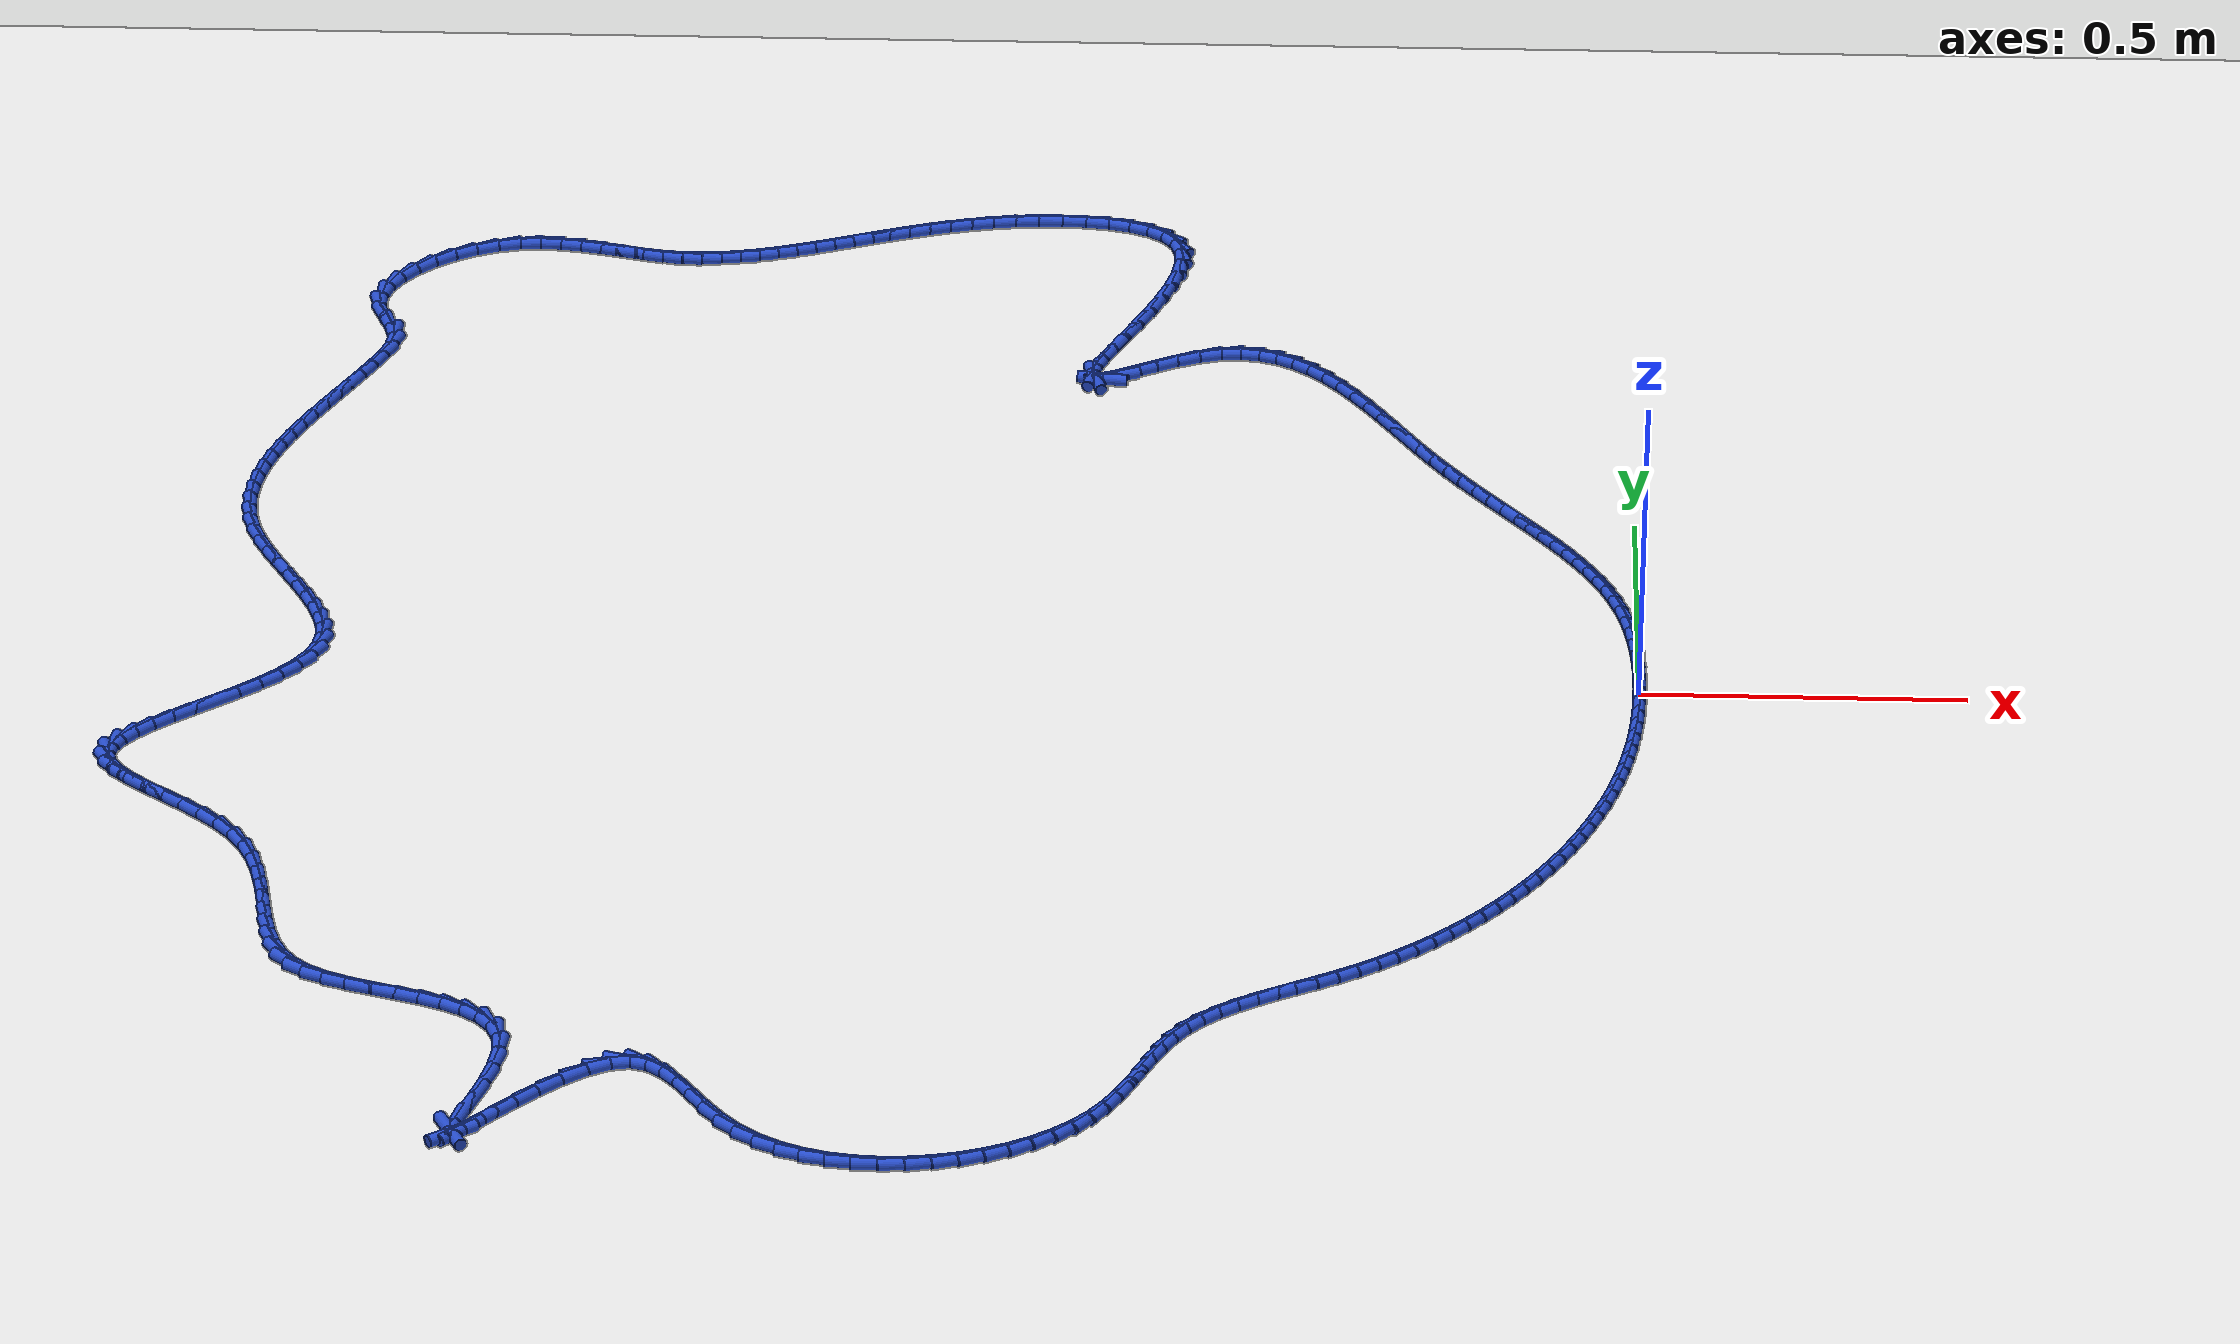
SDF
<sdf version="1.6">
 <world name="default">
  <light name="sun" type="directional">
   <pose>0 0 10 0 -0 0</pose>
   <diffuse>0.8 0.8 0.8 1</diffuse>
   <specular>0.2 0.2 0.2 1</specular>
   <attenuation>
    <range>1000</range>
    <constant>0.9</constant>
    <linear>0.01</linear>
    <quadratic>0.001</quadratic>
   </attenuation>
   <direction>-0.5 0.1 -0.9</direction>
  </light>
  <model name="ground_plane">
   <static>1</static>
   <link name="link">
    <collision name="collision">
     <geometry><plane><normal>0 0 1</normal><size>100 100</size></plane></geometry>
     <surface><friction><ode><mu>100</mu><mu2>50</mu2></ode></friction></surface>
    </collision>
    <visual name="visual">
     <cast_shadows>0</cast_shadows>
     <geometry><plane><normal>0 0 1</normal><size>100 100</size></plane></geometry>
     <material>
      <script><uri>file://media/materials/scripts/gazebo.material</uri><name>Gazebo/WhiteGlow</name></script>
     </material>
    </visual>
   </link>
  </model>
  <gravity>0 0 -9.8</gravity>
  <magnetic_field>6e-06 2.3e-05 -4.2e-05</magnetic_field>
  <atmosphere type="adiabatic"/>
  <physics name="default_physics" default="0" type="ode">
   <max_step_size>0.001</max_step_size>
   <real_time_factor>1</real_time_factor>
   <real_time_update_rate>1000</real_time_update_rate>
  </physics>
  <scene><ambient>0.4 0.4 0.4 1</ambient><background>0.7 0.7 0.7 1</background><shadows>1</shadows></scene>
  <spherical_coordinates>
   <surface_model>EARTH_WGS84</surface_model>
   <latitude_deg>0</latitude_deg>
   <longitude_deg>0</longitude_deg>
   <elevation>0</elevation>
   <heading_deg>0</heading_deg>
  </spherical_coordinates>
  <model name="line">
   <link name="link_0">
    <pose>8.239936510889834e-18 -1.1102230246251565e-16 0.01 0 1.57 -1.568769187980779</pose>
    <collision name="collision">
     <geometry><cylinder><radius>0.01</radius><length>0.08</length></cylinder></geometry>
    </collision>
    <visual name="visual">
     <material>
      <script><name>Gazebo/Blue</name><uri>file://media/materials/scripts/gazebo.material</uri></script>
     </material>
     <geometry><cylinder><radius>0.01</radius><length>0.08</length></cylinder></geometry>
    </visual>
   </link>
   <link name="link_1">
    <pose>-6.884838589907749e-05 0.033963284168576885 0.01 0 1.57 -1.5379115577310962</pose>
    <collision name="collision">
     <geometry><cylinder><radius>0.01</radius><length>0.08</length></cylinder></geometry>
    </collision>
    <visual name="visual">
     <material>
      <script><name>Gazebo/Blue</name><uri>file://media/materials/scripts/gazebo.material</uri></script>
     </material>
     <geometry><cylinder><radius>0.01</radius><length>0.08</length></cylinder></geometry>
    </visual>
   </link>
   <link name="link_2">
    <pose>-0.001187895294535504 0.06798035435918875 0.01 0 1.57 -1.5032869814354892</pose>
    <collision name="collision">
     <geometry><cylinder><radius>0.01</radius><length>0.08</length></cylinder></geometry>
    </collision>
    <visual name="visual">
     <material>
      <script><name>Gazebo/Blue</name><uri>file://media/materials/scripts/gazebo.material</uri></script>
     </material>
     <geometry><cylinder><radius>0.01</radius><length>0.08</length></cylinder></geometry>
    </visual>
   </link>
   <link name="link_3">
    <pose>-0.00347770108287808 0.10184716366132715 0.01 0 1.57 -1.4643409256103015</pose>
    <collision name="collision">
     <geometry><cylinder><radius>0.01</radius><length>0.08</length></cylinder></geometry>
    </collision>
    <visual name="visual">
     <material>
      <script><name>Gazebo/Blue</name><uri>file://media/materials/scripts/gazebo.material</uri></script>
     </material>
     <geometry><cylinder><radius>0.01</radius><length>0.08</length></cylinder></geometry>
    </visual>
   </link>
   <link name="link_4">
    <pose>-0.00705882610789561 0.1353596651644838 0.01 0 1.57 -1.4204263204695051</pose>
    <collision name="collision">
     <geometry><cylinder><radius>0.01</radius><length>0.08</length></cylinder></geometry>
    </collision>
    <visual name="visual">
     <material>
      <script><name>Gazebo/Blue</name><uri>file://media/materials/scripts/gazebo.material</uri></script>
     </material>
     <geometry><cylinder><radius>0.01</radius><length>0.08</length></cylinder></geometry>
    </visual>
   </link>
   <link name="link_5">
    <pose>-0.012051830726556908 0.16831381195815034 0.01 0 1.57 -1.3708006603784892</pose>
    <collision name="collision">
     <geometry><cylinder><radius>0.01</radius><length>0.08</length></cylinder></geometry>
    </collision>
    <visual name="visual">
     <material>
      <script><name>Gazebo/Blue</name><uri>file://media/materials/scripts/gazebo.material</uri></script>
     </material>
     <geometry><cylinder><radius>0.01</radius><length>0.08</length></cylinder></geometry>
    </visual>
   </link>
   <link name="link_6">
    <pose>-0.018577275295830774 0.20050555713181833 0.01 0 1.57 -1.3146332263357112</pose>
    <collision name="collision">
     <geometry><cylinder><radius>0.01</radius><length>0.08</length></cylinder></geometry>
    </collision>
    <visual name="visual">
     <material>
      <script><name>Gazebo/Blue</name><uri>file://media/materials/scripts/gazebo.material</uri></script>
     </material>
     <geometry><cylinder><radius>0.01</radius><length>0.08</length></cylinder></geometry>
    </visual>
   </link>
   <link name="link_7">
    <pose>-0.026755720172686025 0.23173085377497965 0.01 0 1.57 -1.2518290704146458</pose>
    <collision name="collision">
     <geometry><cylinder><radius>0.01</radius><length>0.08</length></cylinder></geometry>
    </collision>
    <visual name="visual">
     <material>
      <script><name>Gazebo/Blue</name><uri>file://media/materials/scripts/gazebo.material</uri></script>
     </material>
     <geometry><cylinder><radius>0.01</radius><length>0.08</length></cylinder></geometry>
    </visual>
   </link>
   <link name="link_8">
    <pose>-0.03668979084973928 0.26181188946625367 0.01 0 1.57 -1.189024689200159</pose>
    <collision name="collision">
     <geometry><cylinder><radius>0.01</radius><length>0.08</length></cylinder></geometry>
    </collision>
    <visual name="visual">
     <material>
      <script><name>Gazebo/Blue</name><uri>file://media/materials/scripts/gazebo.material</uri></script>
     </material>
     <geometry><cylinder><radius>0.01</radius><length>0.08</length></cylinder></geometry>
    </visual>
   </link>
   <link name="link_9">
    <pose>-0.04832680934169417 0.29079802425252177 0.01 0 1.57 -1.1308273459899276</pose>
    <collision name="collision">
     <geometry><cylinder><radius>0.01</radius><length>0.08</length></cylinder></geometry>
    </collision>
    <visual name="visual">
     <material>
      <script><name>Gazebo/Blue</name><uri>file://media/materials/scripts/gazebo.material</uri></script>
     </material>
     <geometry><cylinder><radius>0.01</radius><length>0.08</length></cylinder></geometry>
    </visual>
   </link>
   <link name="link_10">
    <pose>-0.06153446916584447 0.3188550959475751 0.01 0 1.57 -1.0783287872617717</pose>
    <collision name="collision">
     <geometry><cylinder><radius>0.01</radius><length>0.08</length></cylinder></geometry>
    </collision>
    <visual name="visual">
     <material>
      <script><name>Gazebo/Blue</name><uri>file://media/materials/scripts/gazebo.material</uri></script>
     </material>
     <geometry><cylinder><radius>0.01</radius><length>0.08</length></cylinder></geometry>
    </visual>
   </link>
   <link name="link_11">
    <pose>-0.07617981572210636 0.3461498904085217 0.01 0 1.57 -1.0322931298612419</pose>
    <collision name="collision">
     <geometry><cylinder><radius>0.01</radius><length>0.08</length></cylinder></geometry>
    </collision>
    <visual name="visual">
     <material>
      <script><name>Gazebo/Blue</name><uri>file://media/materials/scripts/gazebo.material</uri></script>
     </material>
     <geometry><cylinder><radius>0.01</radius><length>0.08</length></cylinder></geometry>
    </visual>
   </link>
   <link name="link_12">
    <pose>-0.09212989441039607 0.37284919349246987 0.01 0 1.57 -0.9931920147272714</pose>
    <collision name="collision">
     <geometry><cylinder><radius>0.01</radius><length>0.08</length></cylinder></geometry>
    </collision>
    <visual name="visual">
     <material>
      <script><name>Gazebo/Blue</name><uri>file://media/materials/scripts/gazebo.material</uri></script>
     </material>
     <geometry><cylinder><radius>0.01</radius><length>0.08</length></cylinder></geometry>
    </visual>
   </link>
   <link name="link_13">
    <pose>-0.10925175063062981 0.3991197910565278 0.01 0 1.57 -0.9612427282606143</pose>
    <collision name="collision">
     <geometry><cylinder><radius>0.01</radius><length>0.08</length></cylinder></geometry>
    </collision>
    <visual name="visual">
     <material>
      <script><name>Gazebo/Blue</name><uri>file://media/materials/scripts/gazebo.material</uri></script>
     </material>
     <geometry><cylinder><radius>0.01</radius><length>0.08</length></cylinder></geometry>
    </visual>
   </link>
   <link name="link_14">
    <pose>-0.12741242978272382 0.4251284689578037 0.01 0 1.57 -0.9364613109729303</pose>
    <collision name="collision">
     <geometry><cylinder><radius>0.01</radius><length>0.08</length></cylinder></geometry>
    </collision>
    <visual name="visual">
     <material>
      <script><name>Gazebo/Blue</name><uri>file://media/materials/scripts/gazebo.material</uri></script>
     </material>
     <geometry><cylinder><radius>0.01</radius><length>0.08</length></cylinder></geometry>
    </visual>
   </link>
   <link name="link_15">
    <pose>-0.14647897726659428 0.4510420130534058 0.01 0 1.57 -0.918716794172173</pose>
    <collision name="collision">
     <geometry><cylinder><radius>0.01</radius><length>0.08</length></cylinder></geometry>
    </collision>
    <visual name="visual">
     <material>
      <script><name>Gazebo/Blue</name><uri>file://media/materials/scripts/gazebo.material</uri></script>
     </material>
     <geometry><cylinder><radius>0.01</radius><length>0.08</length></cylinder></geometry>
    </visual>
   </link>
   <link name="link_16">
    <pose>-0.16631843848215752 0.4770272092004423 0.01 0 1.57 -0.9077779189172979</pose>
    <collision name="collision">
     <geometry><cylinder><radius>0.01</radius><length>0.08</length></cylinder></geometry>
    </collision>
    <visual name="visual">
     <material>
      <script><name>Gazebo/Blue</name><uri>file://media/materials/scripts/gazebo.material</uri></script>
     </material>
     <geometry><cylinder><radius>0.01</radius><length>0.08</length></cylinder></geometry>
    </visual>
   </link>
   <link name="link_17">
    <pose>-0.1867978588293296 0.5032508432560214 0.01 0 1.57 -0.9033485758834942</pose>
    <collision name="collision">
     <geometry><cylinder><radius>0.01</radius><length>0.08</length></cylinder></geometry>
    </collision>
    <visual name="visual">
     <material>
      <script><name>Gazebo/Blue</name><uri>file://media/materials/scripts/gazebo.material</uri></script>
     </material>
     <geometry><cylinder><radius>0.01</radius><length>0.08</length></cylinder></geometry>
    </visual>
   </link>
   <link name="link_18">
    <pose>-0.2077842837080268 0.5298797010772512 0.01 0 1.57 -0.9050916242084458</pose>
    <collision name="collision">
     <geometry><cylinder><radius>0.01</radius><length>0.08</length></cylinder></geometry>
    </collision>
    <visual name="visual">
     <material>
      <script><name>Gazebo/Blue</name><uri>file://media/materials/scripts/gazebo.material</uri></script>
     </material>
     <geometry><cylinder><radius>0.01</radius><length>0.08</length></cylinder></geometry>
    </visual>
   </link>
   <link name="link_19">
    <pose>-0.2291447585181654 0.5570805685212401 0.01 0 1.57 -0.9126426502276339</pose>
    <collision name="collision">
     <geometry><cylinder><radius>0.01</radius><length>0.08</length></cylinder></geometry>
    </collision>
    <visual name="visual">
     <material>
      <script><name>Gazebo/Blue</name><uri>file://media/materials/scripts/gazebo.material</uri></script>
     </material>
     <geometry><cylinder><radius>0.01</radius><length>0.08</length></cylinder></geometry>
    </visual>
   </link>
   <link name="link_20">
    <pose>-0.2507463286596615 0.5850202314450962 0.01 0 1.57 -0.925616029925873</pose>
    <collision name="collision">
     <geometry><cylinder><radius>0.01</radius><length>0.08</length></cylinder></geometry>
    </collision>
    <visual name="visual">
     <material>
      <script><name>Gazebo/Blue</name><uri>file://media/materials/scripts/gazebo.material</uri></script>
     </material>
     <geometry><cylinder><radius>0.01</radius><length>0.08</length></cylinder></geometry>
    </visual>
   </link>
   <link name="link_21">
    <pose>-0.2724560395324314 0.6138654757059276 0.01 0 1.57 -0.9436058251299823</pose>
    <collision name="collision">
     <geometry><cylinder><radius>0.01</radius><length>0.08</length></cylinder></geometry>
    </collision>
    <visual name="visual">
     <material>
      <script><name>Gazebo/Blue</name><uri>file://media/materials/scripts/gazebo.material</uri></script>
     </material>
     <geometry><cylinder><radius>0.01</radius><length>0.08</length></cylinder></geometry>
    </visual>
   </link>
   <link name="link_22">
    <pose>-0.29414093653639134 0.6437830871608429 0.01 0 1.57 -0.9661839045540002</pose>
    <collision name="collision">
     <geometry><cylinder><radius>0.01</radius><length>0.08</length></cylinder></geometry>
    </collision>
    <visual name="visual">
     <material>
      <script><name>Gazebo/Blue</name><uri>file://media/materials/scripts/gazebo.material</uri></script>
     </material>
     <geometry><cylinder><radius>0.01</radius><length>0.08</length></cylinder></geometry>
    </visual>
   </link>
   <link name="link_23">
    <pose>-0.3156680650714575 0.6749398516669498 0.01 0 1.57 -0.9924007623152327</pose>
    <collision name="collision">
     <geometry><cylinder><radius>0.01</radius><length>0.08</length></cylinder></geometry>
    </collision>
    <visual name="visual">
     <material>
      <script><name>Gazebo/Blue</name><uri>file://media/materials/scripts/gazebo.material</uri></script>
     </material>
     <geometry><cylinder><radius>0.01</radius><length>0.08</length></cylinder></geometry>
    </visual>
   </link>
   <link name="link_24">
    <pose>-0.3369132298268747 0.7074806537702544 0.01 0 1.57 -1.012945403709321</pose>
    <collision name="collision">
     <geometry><cylinder><radius>0.01</radius><length>0.08</length></cylinder></geometry>
    </collision>
    <visual name="visual">
     <material>
      <script><name>Gazebo/Blue</name><uri>file://media/materials/scripts/gazebo.material</uri></script>
     </material>
     <geometry><cylinder><radius>0.01</radius><length>0.08</length></cylinder></geometry>
    </visual>
   </link>
   <link name="link_25">
    <pose>-0.35791595093579703 0.7411410316948477 0.01 0 1.57 -1.020672715207863</pose>
    <collision name="collision">
     <geometry><cylinder><radius>0.01</radius><length>0.08</length></cylinder></geometry>
    </collision>
    <visual name="visual">
     <material>
      <script><name>Gazebo/Blue</name><uri>file://media/materials/scripts/gazebo.material</uri></script>
     </material>
     <geometry><cylinder><radius>0.01</radius><length>0.08</length></cylinder></geometry>
    </visual>
   </link>
   <link name="link_26">
    <pose>-0.3788608896694163 0.7752936196553027 0.01 0 1.57 -1.0159316533496228</pose>
    <collision name="collision">
     <geometry><cylinder><radius>0.01</radius><length>0.08</length></cylinder></geometry>
    </collision>
    <visual name="visual">
     <material>
      <script><name>Gazebo/Blue</name><uri>file://media/materials/scripts/gazebo.material</uri></script>
     </material>
     <geometry><cylinder><radius>0.01</radius><length>0.08</length></cylinder></geometry>
    </visual>
   </link>
   <link name="link_27">
    <pose>-0.39993773483118594 0.8092984812632591 0.01 0 1.57 -0.9985109300481555</pose>
    <collision name="collision">
     <geometry><cylinder><radius>0.01</radius><length>0.08</length></cylinder></geometry>
    </collision>
    <visual name="visual">
     <material>
      <script><name>Gazebo/Blue</name><uri>file://media/materials/scripts/gazebo.material</uri></script>
     </material>
     <geometry><cylinder><radius>0.01</radius><length>0.08</length></cylinder></geometry>
    </visual>
   </link>
   <link name="link_28">
    <pose>-0.42133617522455946 0.8425156801303565 0.01 0 1.57 -0.9673484333405514</pose>
    <collision name="collision">
     <geometry><cylinder><radius>0.01</radius><length>0.08</length></cylinder></geometry>
    </collision>
    <visual name="visual">
     <material>
      <script><name>Gazebo/Blue</name><uri>file://media/materials/scripts/gazebo.material</uri></script>
     </material>
     <geometry><cylinder><radius>0.01</radius><length>0.08</length></cylinder></geometry>
    </visual>
   </link>
   <link name="link_29">
    <pose>-0.4432458996529901 0.8743052798682337 0.01 0 1.57 -0.9204583813876139</pose>
    <collision name="collision">
     <geometry><cylinder><radius>0.01</radius><length>0.08</length></cylinder></geometry>
    </collision>
    <visual name="visual">
     <material>
      <script><name>Gazebo/Blue</name><uri>file://media/materials/scripts/gazebo.material</uri></script>
     </material>
     <geometry><cylinder><radius>0.01</radius><length>0.08</length></cylinder></geometry>
    </visual>
   </link>
   <link name="link_30">
    <pose>-0.4658565969199314 0.9040273440885304 0.01 0 1.57 -0.8548333704648474</pose>
    <collision name="collision">
     <geometry><cylinder><radius>0.01</radius><length>0.08</length></cylinder></geometry>
    </collision>
    <visual name="visual">
     <material>
      <script><name>Gazebo/Blue</name><uri>file://media/materials/scripts/gazebo.material</uri></script>
     </material>
     <geometry><cylinder><radius>0.01</radius><length>0.08</length></cylinder></geometry>
    </visual>
   </link>
   <link name="link_31">
    <pose>-0.48935795582883684 0.9310419364028861 0.01 0 1.57 -0.7664461051331181</pose>
    <collision name="collision">
     <geometry><cylinder><radius>0.01</radius><length>0.08</length></cylinder></geometry>
    </collision>
    <visual name="visual">
     <material>
      <script><name>Gazebo/Blue</name><uri>file://media/materials/scripts/gazebo.material</uri></script>
     </material>
     <geometry><cylinder><radius>0.01</radius><length>0.08</length></cylinder></geometry>
    </visual>
   </link>
   <link name="link_32">
    <pose>-0.5139396651831597 0.9547091204229403 0.01 0 1.57 -0.6506671082119945</pose>
    <collision name="collision">
     <geometry><cylinder><radius>0.01</radius><length>0.08</length></cylinder></geometry>
    </collision>
    <visual name="visual">
     <material>
      <script><name>Gazebo/Blue</name><uri>file://media/materials/scripts/gazebo.material</uri></script>
     </material>
     <geometry><cylinder><radius>0.01</radius><length>0.08</length></cylinder></geometry>
    </visual>
   </link>
   <link name="link_33">
    <pose>-0.5397914137863531 0.974388959760332 0.01 0 1.57 -0.5037211474533001</pose>
    <collision name="collision">
     <geometry><cylinder><radius>0.01</radius><length>0.08</length></cylinder></geometry>
    </collision>
    <visual name="visual">
     <material>
      <script><name>Gazebo/Blue</name><uri>file://media/materials/scripts/gazebo.material</uri></script>
     </material>
     <geometry><cylinder><radius>0.01</radius><length>0.08</length></cylinder></geometry>
    </visual>
   </link>
   <link name="link_34">
    <pose>-0.5671028904418711 0.9894415180267012 0.01 0 1.57 -0.3258380147962835</pose>
    <collision name="collision">
     <geometry><cylinder><radius>0.01</radius><length>0.08</length></cylinder></geometry>
    </collision>
    <visual name="visual">
     <material>
      <script><name>Gazebo/Blue</name><uri>file://media/materials/scripts/gazebo.material</uri></script>
     </material>
     <geometry><cylinder><radius>0.01</radius><length>0.08</length></cylinder></geometry>
    </visual>
   </link>
   <link name="link_35">
    <pose>-0.5960637839531668 0.999226858833687 0.01 0 1.57 -0.12525597777310601</pose>
    <collision name="collision">
     <geometry><cylinder><radius>0.01</radius><length>0.08</length></cylinder></geometry>
    </collision>
    <visual name="visual">
     <material>
      <script><name>Gazebo/Blue</name><uri>file://media/materials/scripts/gazebo.material</uri></script>
     </material>
     <geometry><cylinder><radius>0.01</radius><length>0.08</length></cylinder></geometry>
    </visual>
   </link>
   <link name="link_36">
    <pose>-0.6268637831236935 1.003105045792929 0.01 0 1.57 0.08111923479606854</pose>
    <collision name="collision">
     <geometry><cylinder><radius>0.01</radius><length>0.08</length></cylinder></geometry>
    </collision>
    <visual name="visual">
     <material>
      <script><name>Gazebo/Blue</name><uri>file://media/materials/scripts/gazebo.material</uri></script>
     </material>
     <geometry><cylinder><radius>0.01</radius><length>0.08</length></cylinder></geometry>
    </visual>
   </link>
   <link name="link_37">
    <pose>-0.6596925767569046 1.0004361425160662 0.01 0 1.57 0.27203568665329847</pose>
    <collision name="collision">
     <geometry><cylinder><radius>0.01</radius><length>0.08</length></cylinder></geometry>
    </collision>
    <visual name="visual">
     <material>
      <script><name>Gazebo/Blue</name><uri>file://media/materials/scripts/gazebo.material</uri></script>
     </material>
     <geometry><cylinder><radius>0.01</radius><length>0.08</length></cylinder></geometry>
    </visual>
   </link>
   <link name="link_38">
    <pose>-0.6946826463632483 0.9906756281500523 0.01 0 1.57 0.4054848090594809</pose>
    <collision name="collision">
     <geometry><cylinder><radius>0.01</radius><length>0.08</length></cylinder></geometry>
    </collision>
    <visual name="visual">
     <material>
      <script><name>Gazebo/Blue</name><uri>file://media/materials/scripts/gazebo.material</uri></script>
     </material>
     <geometry><cylinder><radius>0.01</radius><length>0.08</length></cylinder></geometry>
    </visual>
   </link>
   <link name="link_39">
    <pose>-0.7308428938630864 0.9751529902492242 0.01 0 1.57 0.4768607453517932</pose>
    <collision name="collision">
     <geometry><cylinder><radius>0.01</radius><length>0.08</length></cylinder></geometry>
    </collision>
    <visual name="visual">
     <material>
      <script><name>Gazebo/Blue</name><uri>file://media/materials/scripts/gazebo.material</uri></script>
     </material>
     <geometry><cylinder><radius>0.01</radius><length>0.08</length></cylinder></geometry>
    </visual>
   </link>
   <link name="link_40">
    <pose>-0.7661560553736643 0.956909249186225 0.01 0 1.57 0.5036686389816843</pose>
    <collision name="collision">
     <geometry><cylinder><radius>0.01</radius><length>0.08</length></cylinder></geometry>
    </collision>
    <visual name="visual">
     <material>
      <script><name>Gazebo/Blue</name><uri>file://media/materials/scripts/gazebo.material</uri></script>
     </material>
     <geometry><cylinder><radius>0.01</radius><length>0.08</length></cylinder></geometry>
    </visual>
   </link>
   <link name="link_41">
    <pose>-0.7985671927225647 0.939048261946423 0.01 0 1.57 0.4823308693171076</pose>
    <collision name="collision">
     <geometry><cylinder><radius>0.01</radius><length>0.08</length></cylinder></geometry>
    </collision>
    <visual name="visual">
     <material>
      <script><name>Gazebo/Blue</name><uri>file://media/materials/scripts/gazebo.material</uri></script>
     </material>
     <geometry><cylinder><radius>0.01</radius><length>0.08</length></cylinder></geometry>
    </visual>
   </link>
   <link name="link_42">
    <pose>-0.8260213677373713 0.9246738855151878 0.01 0 1.57 0.36382411308853496</pose>
    <collision name="collision">
     <geometry><cylinder><radius>0.01</radius><length>0.08</length></cylinder></geometry>
    </collision>
    <visual name="visual">
     <material>
      <script><name>Gazebo/Blue</name><uri>file://media/materials/scripts/gazebo.material</uri></script>
     </material>
     <geometry><cylinder><radius>0.01</radius><length>0.08</length></cylinder></geometry>
    </visual>
   </link>
   <link name="link_43">
    <pose>-0.8464636422456663 0.9168899768778885 0.01 0 1.57 -0.13613068136068118</pose>
    <collision name="collision">
     <geometry><cylinder><radius>0.01</radius><length>0.08</length></cylinder></geometry>
    </collision>
    <visual name="visual">
     <material>
      <script><name>Gazebo/Blue</name><uri>file://media/materials/scripts/gazebo.material</uri></script>
     </material>
     <geometry><cylinder><radius>0.01</radius><length>0.08</length></cylinder></geometry>
    </visual>
   </link>
   <link name="link_44">
    <pose>-0.8580917203479129 0.9184827662080651 0.01 0 1.57 -1.2954126902794283</pose>
    <collision name="collision">
     <geometry><cylinder><radius>0.01</radius><length>0.08</length></cylinder></geometry>
    </collision>
    <visual name="visual">
     <material>
      <script><name>Gazebo/Blue</name><uri>file://media/materials/scripts/gazebo.material</uri></script>
     </material>
     <geometry><cylinder><radius>0.01</radius><length>0.08</length></cylinder></geometry>
    </visual>
   </link>
   <link name="link_45">
    <pose>-0.8612248944012217 0.929571181385424 0.01 0 1.57 1.3680436797934128</pose>
    <collision name="collision">
     <geometry><cylinder><radius>0.01</radius><length>0.08</length></cylinder></geometry>
    </collision>
    <visual name="visual">
     <material>
      <script><name>Gazebo/Blue</name><uri>file://media/materials/scripts/gazebo.material</uri></script>
     </material>
     <geometry><cylinder><radius>0.01</radius><length>0.08</length></cylinder></geometry>
    </visual>
   </link>
   <link name="link_46">
    <pose>-0.857242913124703 0.9489409237891905 0.01 0 1.57 1.2186955344503692</pose>
    <collision name="collision">
     <geometry><cylinder><radius>0.01</radius><length>0.08</length></cylinder></geometry>
    </collision>
    <visual name="visual">
     <material>
      <script><name>Gazebo/Blue</name><uri>file://media/materials/scripts/gazebo.material</uri></script>
     </material>
     <geometry><cylinder><radius>0.01</radius><length>0.08</length></cylinder></geometry>
    </visual>
   </link>
   <link name="link_47">
    <pose>-0.8475333797222725 0.9753678199865128 0.01 0 1.57 1.160057830518008</pose>
    <collision name="collision">
     <geometry><cylinder><radius>0.01</radius><length>0.08</length></cylinder></geometry>
    </collision>
    <visual name="visual">
     <material>
      <script><name>Gazebo/Blue</name><uri>file://media/materials/scripts/gazebo.material</uri></script>
     </material>
     <geometry><cylinder><radius>0.01</radius><length>0.08</length></cylinder></geometry>
    </visual>
   </link>
   <link name="link_48">
    <pose>-0.8334838973978465 1.007627696544538 0.01 0 1.57 1.1387125407436758</pose>
    <collision name="collision">
     <geometry><cylinder><radius>0.01</radius><length>0.08</length></cylinder></geometry>
    </collision>
    <visual name="visual">
     <material>
      <script><name>Gazebo/Blue</name><uri>file://media/materials/scripts/gazebo.material</uri></script>
     </material>
     <geometry><cylinder><radius>0.01</radius><length>0.08</length></cylinder></geometry>
    </visual>
   </link>
   <link name="link_49">
    <pose>-0.8164820693553405 1.0444963800304152 0.01 0 1.57 1.1386319519810593</pose>
    <collision name="collision">
     <geometry><cylinder><radius>0.01</radius><length>0.08</length></cylinder></geometry>
    </collision>
    <visual name="visual">
     <material>
      <script><name>Gazebo/Blue</name><uri>file://media/materials/scripts/gazebo.material</uri></script>
     </material>
     <geometry><cylinder><radius>0.01</radius><length>0.08</length></cylinder></geometry>
    </visual>
   </link>
   <link name="link_50">
    <pose>-0.7979154987986706 1.0847496970112924 0.01 0 1.57 1.154677800600969</pose>
    <collision name="collision">
     <geometry><cylinder><radius>0.01</radius><length>0.08</length></cylinder></geometry>
    </collision>
    <visual name="visual">
     <material>
      <script><name>Gazebo/Blue</name><uri>file://media/materials/scripts/gazebo.material</uri></script>
     </material>
     <geometry><cylinder><radius>0.01</radius><length>0.08</length></cylinder></geometry>
    </visual>
   </link>
   <link name="link_51">
    <pose>-0.779171788931753 1.1271634740543175 0.01 0 1.57 1.1864534394016635</pose>
    <collision name="collision">
     <geometry><cylinder><radius>0.01</radius><length>0.08</length></cylinder></geometry>
    </collision>
    <visual name="visual">
     <material>
      <script><name>Gazebo/Blue</name><uri>file://media/materials/scripts/gazebo.material</uri></script>
     </material>
     <geometry><cylinder><radius>0.01</radius><length>0.08</length></cylinder></geometry>
    </visual>
   </link>
   <link name="link_52">
    <pose>-0.7616385429585033 1.170513537726638 0.01 0 1.57 1.2369499213273858</pose>
    <collision name="collision">
     <geometry><cylinder><radius>0.01</radius><length>0.08</length></cylinder></geometry>
    </collision>
    <visual name="visual">
     <material>
      <script><name>Gazebo/Blue</name><uri>file://media/materials/scripts/gazebo.material</uri></script>
     </material>
     <geometry><cylinder><radius>0.01</radius><length>0.08</length></cylinder></geometry>
    </visual>
   </link>
   <link name="link_53">
    <pose>-0.7467033640828377 1.2135757145954023 0.01 0 1.57 1.3131289967814044</pose>
    <collision name="collision">
     <geometry><cylinder><radius>0.01</radius><length>0.08</length></cylinder></geometry>
    </collision>
    <visual name="visual">
     <material>
      <script><name>Gazebo/Blue</name><uri>file://media/materials/scripts/gazebo.material</uri></script>
     </material>
     <geometry><cylinder><radius>0.01</radius><length>0.08</length></cylinder></geometry>
    </visual>
   </link>
   <link name="link_54">
    <pose>-0.7357538555086721 1.2551258312277587 0.01 0 1.57 1.428106688193839</pose>
    <collision name="collision">
     <geometry><cylinder><radius>0.01</radius><length>0.08</length></cylinder></geometry>
    </collision>
    <visual name="visual">
     <material>
      <script><name>Gazebo/Blue</name><uri>file://media/materials/scripts/gazebo.material</uri></script>
     </material>
     <geometry><cylinder><radius>0.01</radius><length>0.08</length></cylinder></geometry>
    </visual>
   </link>
   <link name="link_55">
    <pose>-0.7301776204399222 1.2939397141908553 0.01 0 1.57 -1.5368202100542399</pose>
    <collision name="collision">
     <geometry><cylinder><radius>0.01</radius><length>0.08</length></cylinder></geometry>
    </collision>
    <visual name="visual">
     <material>
      <script><name>Gazebo/Blue</name><uri>file://media/materials/scripts/gazebo.material</uri></script>
     </material>
     <geometry><cylinder><radius>0.01</radius><length>0.08</length></cylinder></geometry>
    </visual>
   </link>
   <link name="link_56">
    <pose>-0.7313622620805044 1.3287931900518395 0.01 0 1.57 -1.2662243334112948</pose>
    <collision name="collision">
     <geometry><cylinder><radius>0.01</radius><length>0.08</length></cylinder></geometry>
    </collision>
    <visual name="visual">
     <material>
      <script><name>Gazebo/Blue</name><uri>file://media/materials/scripts/gazebo.material</uri></script>
     </material>
     <geometry><cylinder><radius>0.01</radius><length>0.08</length></cylinder></geometry>
    </visual>
   </link>
   <link name="link_57">
    <pose>-0.7406898170902045 1.3584654346496763 0.01 0 1.57 -0.9237892005091377</pose>
    <collision name="collision">
     <geometry><cylinder><radius>0.01</radius><length>0.08</length></cylinder></geometry>
    </collision>
    <visual name="visual">
     <material>
      <script><name>Gazebo/Blue</name><uri>file://media/materials/scripts/gazebo.material</uri></script>
     </material>
     <geometry><cylinder><radius>0.01</radius><length>0.08</length></cylinder></geometry>
    </visual>
   </link>
   <link name="link_58">
    <pose>-0.7586677996104176 1.3822618055180071 0.01 0 1.57 -0.6264146758860445</pose>
    <collision name="collision">
     <geometry><cylinder><radius>0.01</radius><length>0.08</length></cylinder></geometry>
    </collision>
    <visual name="visual">
     <material>
      <script><name>Gazebo/Blue</name><uri>file://media/materials/scripts/gazebo.material</uri></script>
     </material>
     <geometry><cylinder><radius>0.01</radius><length>0.08</length></cylinder></geometry>
    </visual>
   </link>
   <link name="link_59">
    <pose>-0.7839847444725382 1.4005821015522353 0.01 0 1.57 -0.4060967333364357</pose>
    <collision name="collision">
     <geometry><cylinder><radius>0.01</radius><length>0.08</length></cylinder></geometry>
    </collision>
    <visual name="visual">
     <material>
      <script><name>Gazebo/Blue</name><uri>file://media/materials/scripts/gazebo.material</uri></script>
     </material>
     <geometry><cylinder><radius>0.01</radius><length>0.08</length></cylinder></geometry>
    </visual>
   </link>
   <link name="link_60">
    <pose>-0.8151023318736438 1.4139626152810536 0.01 0 1.57 -0.2484882658438684</pose>
    <collision name="collision">
     <geometry><cylinder><radius>0.01</radius><length>0.08</length></cylinder></geometry>
    </collision>
    <visual name="visual">
     <material>
      <script><name>Gazebo/Blue</name><uri>file://media/materials/scripts/gazebo.material</uri></script>
     </material>
     <geometry><cylinder><radius>0.01</radius><length>0.08</length></cylinder></geometry>
    </visual>
   </link>
   <link name="link_61">
    <pose>-0.8504822420108137 1.4229396392331568 0.01 0 1.57 -0.13330710241600108</pose>
    <collision name="collision">
     <geometry><cylinder><radius>0.01</radius><length>0.08</length></cylinder></geometry>
    </collision>
    <visual name="visual">
     <material>
      <script><name>Gazebo/Blue</name><uri>file://media/materials/scripts/gazebo.material</uri></script>
     </material>
     <geometry><cylinder><radius>0.01</radius><length>0.08</length></cylinder></geometry>
    </visual>
   </link>
   <link name="link_62">
    <pose>-0.8885861550811256 1.4280494659372367 0.01 0 1.57 -0.04524627482929764</pose>
    <collision name="collision">
     <geometry><cylinder><radius>0.01</radius><length>0.08</length></cylinder></geometry>
    </collision>
    <visual name="visual">
     <material>
      <script><name>Gazebo/Blue</name><uri>file://media/materials/scripts/gazebo.material</uri></script>
     </material>
     <geometry><cylinder><radius>0.01</radius><length>0.08</length></cylinder></geometry>
    </visual>
   </link>
   <link name="link_63">
    <pose>-0.9278757512816587 1.4298283879219882 0.01 0 1.57 0.026151628441838427</pose>
    <collision name="collision">
     <geometry><cylinder><radius>0.01</radius><length>0.08</length></cylinder></geometry>
    </collision>
    <visual name="visual">
     <material>
      <script><name>Gazebo/Blue</name><uri>file://media/materials/scripts/gazebo.material</uri></script>
     </material>
     <geometry><cylinder><radius>0.01</radius><length>0.08</length></cylinder></geometry>
    </visual>
   </link>
   <link name="link_64">
    <pose>-0.9668351853711411 1.4288093029467723 0.01 0 1.57 0.08942881015920927</pose>
    <collision name="collision">
     <geometry><cylinder><radius>0.01</radius><length>0.08</length></cylinder></geometry>
    </collision>
    <visual name="visual">
     <material>
      <script><name>Gazebo/Blue</name><uri>file://media/materials/scripts/gazebo.material</uri></script>
     </material>
     <geometry><cylinder><radius>0.01</radius><length>0.08</length></cylinder></geometry>
    </visual>
   </link>
   <link name="link_65">
    <pose>-1.0046604194305342 1.4254175906931563 0.01 0 1.57 0.14773920661736598</pose>
    <collision name="collision">
     <geometry><cylinder><radius>0.01</radius><length>0.08</length></cylinder></geometry>
    </collision>
    <visual name="visual">
     <material>
      <script><name>Gazebo/Blue</name><uri>file://media/materials/scripts/gazebo.material</uri></script>
     </material>
     <geometry><cylinder><radius>0.01</radius><length>0.08</length></cylinder></geometry>
    </visual>
   </link>
   <link name="link_66">
    <pose>-1.0413880064389314 1.4199516600814435 0.01 0 1.57 0.20024958839547014</pose>
    <collision name="collision">
     <geometry><cylinder><radius>0.01</radius><length>0.08</length></cylinder></geometry>
    </collision>
    <visual name="visual">
     <material>
      <script><name>Gazebo/Blue</name><uri>file://media/materials/scripts/gazebo.material</uri></script>
     </material>
     <geometry><cylinder><radius>0.01</radius><length>0.08</length></cylinder></geometry>
    </visual>
   </link>
   <link name="link_67">
    <pose>-1.0771029541486095 1.412702600966916 0.01 0 1.57 0.24617600146239157</pose>
    <collision name="collision">
     <geometry><cylinder><radius>0.01</radius><length>0.08</length></cylinder></geometry>
    </collision>
    <visual name="visual">
     <material>
      <script><name>Gazebo/Blue</name><uri>file://media/materials/scripts/gazebo.material</uri></script>
     </material>
     <geometry><cylinder><radius>0.01</radius><length>0.08</length></cylinder></geometry>
    </visual>
   </link>
   <link name="link_68">
    <pose>-1.1118902703118472 1.403961503204858 0.01 0 1.57 0.28492077158834617</pose>
    <collision name="collision">
     <geometry><cylinder><radius>0.01</radius><length>0.08</length></cylinder></geometry>
    </collision>
    <visual name="visual">
     <material>
      <script><name>Gazebo/Blue</name><uri>file://media/materials/scripts/gazebo.material</uri></script>
     </material>
     <geometry><cylinder><radius>0.01</radius><length>0.08</length></cylinder></geometry>
    </visual>
   </link>
   <link name="link_69">
    <pose>-1.145834962680922 1.394019456650552 0.01 0 1.57 0.3160324577656235</pose>
    <collision name="collision">
     <geometry><cylinder><radius>0.01</radius><length>0.08</length></cylinder></geometry>
    </collision>
    <visual name="visual">
     <material>
      <script><name>Gazebo/Blue</name><uri>file://media/materials/scripts/gazebo.material</uri></script>
     </material>
     <geometry><cylinder><radius>0.01</radius><length>0.08</length></cylinder></geometry>
    </visual>
   </link>
   <link name="link_70">
    <pose>-1.1790220390081132 1.3831675511592807 0.01 0 1.57 0.3391553161864147</pose>
    <collision name="collision">
     <geometry><cylinder><radius>0.01</radius><length>0.08</length></cylinder></geometry>
    </collision>
    <visual name="visual">
     <material>
      <script><name>Gazebo/Blue</name><uri>file://media/materials/scripts/gazebo.material</uri></script>
     </material>
     <geometry><cylinder><radius>0.01</radius><length>0.08</length></cylinder></geometry>
    </visual>
   </link>
   <link name="link_71">
    <pose>-1.2115365070456976 1.3716968765863278 0.01 0 1.57 0.3539779828538775</pose>
    <collision name="collision">
     <geometry><cylinder><radius>0.01</radius><length>0.08</length></cylinder></geometry>
    </collision>
    <visual name="visual">
     <material>
      <script><name>Gazebo/Blue</name><uri>file://media/materials/scripts/gazebo.material</uri></script>
     </material>
     <geometry><cylinder><radius>0.01</radius><length>0.08</length></cylinder></geometry>
    </visual>
   </link>
   <link name="link_72">
    <pose>-1.2434633745459542 1.359898522786976 0.01 0 1.57 0.360188315180611</pose>
    <collision name="collision">
     <geometry><cylinder><radius>0.01</radius><length>0.08</length></cylinder></geometry>
    </collision>
    <visual name="visual">
     <material>
      <script><name>Gazebo/Blue</name><uri>file://media/materials/scripts/gazebo.material</uri></script>
     </material>
     <geometry><cylinder><radius>0.01</radius><length>0.08</length></cylinder></geometry>
    </visual>
   </link>
   <link name="link_73">
    <pose>-1.2748876492611605 1.348063579616509 0.01 0 1.57 0.3574392197849283</pose>
    <collision name="collision">
     <geometry><cylinder><radius>0.01</radius><length>0.08</length></cylinder></geometry>
    </collision>
    <visual name="visual">
     <material>
      <script><name>Gazebo/Blue</name><uri>file://media/materials/scripts/gazebo.material</uri></script>
     </material>
     <geometry><cylinder><radius>0.01</radius><length>0.08</length></cylinder></geometry>
    </visual>
   </link>
   <link name="link_74">
    <pose>-1.3058943389435946 1.3364831369302088 0.01 0 1.57 0.3453296390945617</pose>
    <collision name="collision">
     <geometry><cylinder><radius>0.01</radius><length>0.08</length></cylinder></geometry>
    </collision>
    <visual name="visual">
     <material>
      <script><name>Gazebo/Blue</name><uri>file://media/materials/scripts/gazebo.material</uri></script>
     </material>
     <geometry><cylinder><radius>0.01</radius><length>0.08</length></cylinder></geometry>
    </visual>
   </link>
   <link name="link_75">
    <pose>-1.3365684513455347 1.3254482845833586 0.01 0 1.57 0.32340582705658283</pose>
    <collision name="collision">
     <geometry><cylinder><radius>0.01</radius><length>0.08</length></cylinder></geometry>
    </collision>
    <visual name="visual">
     <material>
      <script><name>Gazebo/Blue</name><uri>file://media/materials/scripts/gazebo.material</uri></script>
     </material>
     <geometry><cylinder><radius>0.01</radius><length>0.08</length></cylinder></geometry>
    </visual>
   </link>
   <link name="link_76">
    <pose>-1.3669949942192594 1.3152501124312428 0.01 0 1.57 0.29119024301775015</pose>
    <collision name="collision">
     <geometry><cylinder><radius>0.01</radius><length>0.08</length></cylinder></geometry>
    </collision>
    <visual name="visual">
     <material>
      <script><name>Gazebo/Blue</name><uri>file://media/materials/scripts/gazebo.material</uri></script>
     </material>
     <geometry><cylinder><radius>0.01</radius><length>0.08</length></cylinder></geometry>
    </visual>
   </link>
   <link name="link_77">
    <pose>-1.3972589753170461 1.3061797103291428 0.01 0 1.57 0.2482477379413241</pose>
    <collision name="collision">
     <geometry><cylinder><radius>0.01</radius><length>0.08</length></cylinder></geometry>
    </collision>
    <visual name="visual">
     <material>
      <script><name>Gazebo/Blue</name><uri>file://media/materials/scripts/gazebo.material</uri></script>
     </material>
     <geometry><cylinder><radius>0.01</radius><length>0.08</length></cylinder></geometry>
    </visual>
   </link>
   <link name="link_78">
    <pose>-1.4274454023911733 1.2985281681323426 0.01 0 1.57 0.19429879111260154</pose>
    <collision name="collision">
     <geometry><cylinder><radius>0.01</radius><length>0.08</length></cylinder></geometry>
    </collision>
    <visual name="visual">
     <material>
      <script><name>Gazebo/Blue</name><uri>file://media/materials/scripts/gazebo.material</uri></script>
     </material>
     <geometry><cylinder><radius>0.01</radius><length>0.08</length></cylinder></geometry>
    </visual>
   </link>
   <link name="link_79">
    <pose>-1.4576392831939189 1.2925865756961252 0.01 0 1.57 0.12938307136082536</pose>
    <collision name="collision">
     <geometry><cylinder><radius>0.01</radius><length>0.08</length></cylinder></geometry>
    </collision>
    <visual name="visual">
     <material>
      <script><name>Gazebo/Blue</name><uri>file://media/materials/scripts/gazebo.material</uri></script>
     </material>
     <geometry><cylinder><radius>0.01</radius><length>0.08</length></cylinder></geometry>
    </visual>
   </link>
   <link name="link_80">
    <pose>-1.487925625477561 1.2886460228757732 0.01 0 1.57 0.05405815077254932</pose>
    <collision name="collision">
     <geometry><cylinder><radius>0.01</radius><length>0.08</length></cylinder></geometry>
    </collision>
    <visual name="visual">
     <material>
      <script><name>Gazebo/Blue</name><uri>file://media/materials/scripts/gazebo.material</uri></script>
     </material>
     <geometry><cylinder><radius>0.01</radius><length>0.08</length></cylinder></geometry>
    </visual>
   </link>
   <link name="link_81">
    <pose>-1.5183894369943778 1.2869975995265701 0.01 0 1.57 -0.03041394758973531</pose>
    <collision name="collision">
     <geometry><cylinder><radius>0.01</radius><length>0.08</length></cylinder></geometry>
    </collision>
    <visual name="visual">
     <material>
      <script><name>Gazebo/Blue</name><uri>file://media/materials/scripts/gazebo.material</uri></script>
     </material>
     <geometry><cylinder><radius>0.01</radius><length>0.08</length></cylinder></geometry>
    </visual>
   </link>
   <link name="link_82">
    <pose>-1.5491157254966472 1.2879323955037985 0.01 0 1.57 -0.12166443649627862</pose>
    <collision name="collision">
     <geometry><cylinder><radius>0.01</radius><length>0.08</length></cylinder></geometry>
    </collision>
    <visual name="visual">
     <material>
      <script><name>Gazebo/Blue</name><uri>file://media/materials/scripts/gazebo.material</uri></script>
     </material>
     <geometry><cylinder><radius>0.01</radius><length>0.08</length></cylinder></geometry>
    </visual>
   </link>
   <link name="link_83">
    <pose>-1.5801891460672919 1.291731690250548 0.01 0 1.57 -0.20006381642580642</pose>
    <collision name="collision">
     <geometry><cylinder><radius>0.01</radius><length>0.08</length></cylinder></geometry>
    </collision>
    <visual name="visual">
     <material>
      <script><name>Gazebo/Blue</name><uri>file://media/materials/scripts/gazebo.material</uri></script>
     </material>
     <geometry><cylinder><radius>0.01</radius><length>0.08</length></cylinder></geometry>
    </visual>
   </link>
   <link name="link_84">
    <pose>-1.6116741994632517 1.298116118396443 0.01 0 1.57 -0.24067904531085976</pose>
    <collision name="collision">
     <geometry><cylinder><radius>0.01</radius><length>0.08</length></cylinder></geometry>
    </collision>
    <visual name="visual">
     <material>
      <script><name>Gazebo/Blue</name><uri>file://media/materials/scripts/gazebo.material</uri></script>
     </material>
     <geometry><cylinder><radius>0.01</radius><length>0.08</length></cylinder></geometry>
    </visual>
   </link>
   <link name="link_85">
    <pose>-1.6436047122618178 1.3059530327622997 0.01 0 1.57 -0.24449514926126942</pose>
    <collision name="collision">
     <geometry><cylinder><radius>0.01</radius><length>0.08</length></cylinder></geometry>
    </collision>
    <visual name="visual">
     <material>
      <script><name>Gazebo/Blue</name><uri>file://media/materials/scripts/gazebo.material</uri></script>
     </material>
     <geometry><cylinder><radius>0.01</radius><length>0.08</length></cylinder></geometry>
    </visual>
   </link>
   <link name="link_86">
    <pose>-1.6760119373523736 1.3140381923692708 0.01 0 1.57 -0.21329723469604714</pose>
    <collision name="collision">
     <geometry><cylinder><radius>0.01</radius><length>0.08</length></cylinder></geometry>
    </collision>
    <visual name="visual">
     <material>
      <script><name>Gazebo/Blue</name><uri>file://media/materials/scripts/gazebo.material</uri></script>
     </material>
     <geometry><cylinder><radius>0.01</radius><length>0.08</length></cylinder></geometry>
    </visual>
   </link>
   <link name="link_87">
    <pose>-1.7089271276243019 1.3211673562385096 0.01 0 1.57 -0.14745034444127952</pose>
    <collision name="collision">
     <geometry><cylinder><radius>0.01</radius><length>0.08</length></cylinder></geometry>
    </collision>
    <visual name="visual">
     <material>
      <script><name>Gazebo/Blue</name><uri>file://media/materials/scripts/gazebo.material</uri></script>
     </material>
     <geometry><cylinder><radius>0.01</radius><length>0.08</length></cylinder></geometry>
    </visual>
   </link>
   <link name="link_88">
    <pose>-1.7423815359669854 1.3261362833911685 0.01 0 1.57 -0.04712027934115121</pose>
    <collision name="collision">
     <geometry><cylinder><radius>0.01</radius><length>0.08</length></cylinder></geometry>
    </collision>
    <visual name="visual">
     <material>
      <script><name>Gazebo/Blue</name><uri>file://media/materials/scripts/gazebo.material</uri></script>
     </material>
     <geometry><cylinder><radius>0.01</radius><length>0.08</length></cylinder></geometry>
    </visual>
   </link>
   <link name="link_89">
    <pose>-1.7764064152698085 1.3277407328484012 0.01 0 1.57 0.0853984913308995</pose>
    <collision name="collision">
     <geometry><cylinder><radius>0.01</radius><length>0.08</length></cylinder></geometry>
    </collision>
    <visual name="visual">
     <material>
      <script><name>Gazebo/Blue</name><uri>file://media/materials/scripts/gazebo.material</uri></script>
     </material>
     <geometry><cylinder><radius>0.01</radius><length>0.08</length></cylinder></geometry>
    </visual>
   </link>
   <link name="link_90">
    <pose>-1.8110330184221537 1.3247764636313597 0.01 0 1.57 0.240658796452488</pose>
    <collision name="collision">
     <geometry><cylinder><radius>0.01</radius><length>0.08</length></cylinder></geometry>
    </collision>
    <visual name="visual">
     <material>
      <script><name>Gazebo/Blue</name><uri>file://media/materials/scripts/gazebo.material</uri></script>
     </material>
     <geometry><cylinder><radius>0.01</radius><length>0.08</length></cylinder></geometry>
    </visual>
   </link>
   <link name="link_91">
    <pose>-1.8462298797028256 1.3161386236423804 0.01 0 1.57 0.3871668092276538</pose>
    <collision name="collision">
     <geometry><cylinder><radius>0.01</radius><length>0.08</length></cylinder></geometry>
    </collision>
    <visual name="visual">
     <material>
      <script><name>Gazebo/Blue</name><uri>file://media/materials/scripts/gazebo.material</uri></script>
     </material>
     <geometry><cylinder><radius>0.01</radius><length>0.08</length></cylinder></geometry>
    </visual>
   </link>
   <link name="link_92">
    <pose>-1.8812474271824393 1.301860328795884 0.01 0 1.57 0.5178496028419197</pose>
    <collision name="collision">
     <geometry><cylinder><radius>0.01</radius><length>0.08</length></cylinder></geometry>
    </collision>
    <visual name="visual">
     <material>
      <script><name>Gazebo/Blue</name><uri>file://media/materials/scripts/gazebo.material</uri></script>
     </material>
     <geometry><cylinder><radius>0.01</radius><length>0.08</length></cylinder></geometry>
    </visual>
   </link>
   <link name="link_93">
    <pose>-1.9148779638022297 1.2827006763957132 0.01 0 1.57 0.6434775752650339</pose>
    <collision name="collision">
     <geometry><cylinder><radius>0.01</radius><length>0.08</length></cylinder></geometry>
    </collision>
    <visual name="visual">
     <material>
      <script><name>Gazebo/Blue</name><uri>file://media/materials/scripts/gazebo.material</uri></script>
     </material>
     <geometry><cylinder><radius>0.01</radius><length>0.08</length></cylinder></geometry>
    </visual>
   </link>
   <link name="link_94">
    <pose>-1.9459063860005008 1.2594305006772637 0.01 0 1.57 0.7742256912791825</pose>
    <collision name="collision">
     <geometry><cylinder><radius>0.01</radius><length>0.08</length></cylinder></geometry>
    </collision>
    <visual name="visual">
     <material>
      <script><name>Gazebo/Blue</name><uri>file://media/materials/scripts/gazebo.material</uri></script>
     </material>
     <geometry><cylinder><radius>0.01</radius><length>0.08</length></cylinder></geometry>
    </visual>
   </link>
   <link name="link_95">
    <pose>-1.973117590215557 1.2328206358759335 0.01 0 1.57 0.9208594983471085</pose>
    <collision name="collision">
     <geometry><cylinder><radius>0.01</radius><length>0.08</length></cylinder></geometry>
    </collision>
    <visual name="visual">
     <material>
      <script><name>Gazebo/Blue</name><uri>file://media/materials/scripts/gazebo.material</uri></script>
     </material>
     <geometry><cylinder><radius>0.01</radius><length>0.08</length></cylinder></geometry>
    </visual>
   </link>
   <link name="link_96">
    <pose>-1.9952964728857023 1.2036419162271188 0.01 0 1.57 1.0957712082285964</pose>
    <collision name="collision">
     <geometry><cylinder><radius>0.01</radius><length>0.08</length></cylinder></geometry>
    </collision>
    <visual name="visual">
     <material>
      <script><name>Gazebo/Blue</name><uri>file://media/materials/scripts/gazebo.material</uri></script>
     </material>
     <geometry><cylinder><radius>0.01</radius><length>0.08</length></cylinder></geometry>
    </visual>
   </link>
   <link name="link_97">
    <pose>-2.011227930449242 1.1726651759662166 0.01 0 1.57 1.3121042401692884</pose>
    <collision name="collision">
     <geometry><cylinder><radius>0.01</radius><length>0.08</length></cylinder></geometry>
    </collision>
    <visual name="visual">
     <material>
      <script><name>Gazebo/Blue</name><uri>file://media/materials/scripts/gazebo.material</uri></script>
     </material>
     <geometry><cylinder><radius>0.01</radius><length>0.08</length></cylinder></geometry>
    </visual>
   </link>
   <link name="link_98">
    <pose>-2.01969685934448 1.140661249328624 0.01 0 1.57 -1.5643270577389643</pose>
    <collision name="collision">
     <geometry><cylinder><radius>0.01</radius><length>0.08</length></cylinder></geometry>
    </collision>
    <visual name="visual">
     <material>
      <script><name>Gazebo/Blue</name><uri>file://media/materials/scripts/gazebo.material</uri></script>
     </material>
     <geometry><cylinder><radius>0.01</radius><length>0.08</length></cylinder></geometry>
    </visual>
   </link>
   <link name="link_99">
    <pose>-2.01948815600972 1.1084009705497369 0.01 0 1.57 -1.2876761706775792</pose>
    <collision name="collision">
     <geometry><cylinder><radius>0.01</radius><length>0.08</length></cylinder></geometry>
    </collision>
    <visual name="visual">
     <material>
      <script><name>Gazebo/Blue</name><uri>file://media/materials/scripts/gazebo.material</uri></script>
     </material>
     <geometry><cylinder><radius>0.01</radius><length>0.08</length></cylinder></geometry>
    </visual>
   </link>
   <link name="link_100">
    <pose>-2.0102221605240818 1.0765520050248378 0.01 0 1.57 -1.1882393277485575</pose>
    <collision name="collision">
     <geometry><cylinder><radius>0.01</radius><length>0.08</length></cylinder></geometry>
    </collision>
    <visual name="visual">
     <material>
      <script><name>Gazebo/Blue</name><uri>file://media/materials/scripts/gazebo.material</uri></script>
     </material>
     <geometry><cylinder><radius>0.01</radius><length>0.08</length></cylinder></geometry>
    </visual>
   </link>
   <link name="link_101">
    <pose>-1.9975416574290348 1.0450383071680152 0.01 0 1.57 -1.3283106986850373</pose>
    <collision name="collision">
     <geometry><cylinder><radius>0.01</radius><length>0.08</length></cylinder></geometry>
    </collision>
    <visual name="visual">
     <material>
      <script><name>Gazebo/Blue</name><uri>file://media/materials/scripts/gazebo.material</uri></script>
     </material>
     <geometry><cylinder><radius>0.01</radius><length>0.08</length></cylinder></geometry>
    </visual>
   </link>
   <link name="link_102">
    <pose>-1.9897301098258722 1.01345771551749 0.01 0 1.57 1.4799025139721484</pose>
    <collision name="collision">
     <geometry><cylinder><radius>0.01</radius><length>0.08</length></cylinder></geometry>
    </collision>
    <visual name="visual">
     <material>
      <script><name>Gazebo/Blue</name><uri>file://media/materials/scripts/gazebo.material</uri></script>
     </material>
     <geometry><cylinder><radius>0.01</radius><length>0.08</length></cylinder></geometry>
    </visual>
   </link>
   <link name="link_103">
    <pose>-1.9926409861255556 0.9815209362914299 0.01 0 1.57 1.240195005903558</pose>
    <collision name="collision">
     <geometry><cylinder><radius>0.01</radius><length>0.08</length></cylinder></geometry>
    </collision>
    <visual name="visual">
     <material>
      <script><name>Gazebo/Blue</name><uri>file://media/materials/scripts/gazebo.material</uri></script>
     </material>
     <geometry><cylinder><radius>0.01</radius><length>0.08</length></cylinder></geometry>
    </visual>
   </link>
   <link name="link_104">
    <pose>-2.003687544231734 0.9493337024227834 0.01 0 1.57 1.1406327245071728</pose>
    <collision name="collision">
     <geometry><cylinder><radius>0.01</radius><length>0.08</length></cylinder></geometry>
    </collision>
    <visual name="visual">
     <material>
      <script><name>Gazebo/Blue</name><uri>file://media/materials/scripts/gazebo.material</uri></script>
     </material>
     <geometry><cylinder><radius>0.01</radius><length>0.08</length></cylinder></geometry>
    </visual>
   </link>
   <link name="link_105">
    <pose>-2.0184834375739076 0.9170859278600055 0.01 0 1.57 1.1180852872813716</pose>
    <collision name="collision">
     <geometry><cylinder><radius>0.01</radius><length>0.08</length></cylinder></geometry>
    </collision>
    <visual name="visual">
     <material>
      <script><name>Gazebo/Blue</name><uri>file://media/materials/scripts/gazebo.material</uri></script>
     </material>
     <geometry><cylinder><radius>0.01</radius><length>0.08</length></cylinder></geometry>
    </visual>
   </link>
   <link name="link_106">
    <pose>-2.0341414988511515 0.8848943950570576 0.01 0 1.57 1.108263560239242</pose>
    <collision name="collision">
     <geometry><cylinder><radius>0.01</radius><length>0.08</length></cylinder></geometry>
    </collision>
    <visual name="visual">
     <material>
      <script><name>Gazebo/Blue</name><uri>file://media/materials/scripts/gazebo.material</uri></script>
     </material>
     <geometry><cylinder><radius>0.01</radius><length>0.08</length></cylinder></geometry>
    </visual>
   </link>
   <link name="link_107">
    <pose>-2.050164282670978 0.8527593133947972 0.01 0 1.57 1.1056758337423507</pose>
    <collision name="collision">
     <geometry><cylinder><radius>0.01</radius><length>0.08</length></cylinder></geometry>
    </collision>
    <visual name="visual">
     <material>
      <script><name>Gazebo/Blue</name><uri>file://media/materials/scripts/gazebo.material</uri></script>
     </material>
     <geometry><cylinder><radius>0.01</radius><length>0.08</length></cylinder></geometry>
    </visual>
   </link>
   <link name="link_108">
    <pose>-2.06626782260153 0.8206704785325548 0.01 0 1.57 1.110300139176071</pose>
    <collision name="collision">
     <geometry><cylinder><radius>0.01</radius><length>0.08</length></cylinder></geometry>
    </collision>
    <visual name="visual">
     <material>
      <script><name>Gazebo/Blue</name><uri>file://media/materials/scripts/gazebo.material</uri></script>
     </material>
     <geometry><cylinder><radius>0.01</radius><length>0.08</length></cylinder></geometry>
    </visual>
   </link>
   <link name="link_109">
    <pose>-2.082168152210949 0.7886176861296598 0.01 0 1.57 1.1222563259423115</pose>
    <collision name="collision">
     <geometry><cylinder><radius>0.01</radius><length>0.08</length></cylinder></geometry>
    </collision>
    <visual name="visual">
     <material>
      <script><name>Gazebo/Blue</name><uri>file://media/materials/scripts/gazebo.material</uri></script>
     </material>
     <geometry><cylinder><radius>0.01</radius><length>0.08</length></cylinder></geometry>
    </visual>
   </link>
   <link name="link_110">
    <pose>-2.097581305067378 0.7565907318454416 0.01 0 1.57 1.1418048076874483</pose>
    <collision name="collision">
     <geometry><cylinder><radius>0.01</radius><length>0.08</length></cylinder></geometry>
    </collision>
    <visual name="visual">
     <material>
      <script><name>Gazebo/Blue</name><uri>file://media/materials/scripts/gazebo.material</uri></script>
     </material>
     <geometry><cylinder><radius>0.01</radius><length>0.08</length></cylinder></geometry>
    </visual>
   </link>
   <link name="link_111">
    <pose>-2.1122233147389577 0.7245794113392308 0.01 0 1.57 1.1693386892766775</pose>
    <collision name="collision">
     <geometry><cylinder><radius>0.01</radius><length>0.08</length></cylinder></geometry>
    </collision>
    <visual name="visual">
     <material>
      <script><name>Gazebo/Blue</name><uri>file://media/materials/scripts/gazebo.material</uri></script>
     </material>
     <geometry><cylinder><radius>0.01</radius><length>0.08</length></cylinder></geometry>
    </visual>
   </link>
   <link name="link_112">
    <pose>-2.125810214793833 0.6925735202703571 0.01 0 1.57 1.2053645450298898</pose>
    <collision name="collision">
     <geometry><cylinder><radius>0.01</radius><length>0.08</length></cylinder></geometry>
    </collision>
    <visual name="visual">
     <material>
      <script><name>Gazebo/Blue</name><uri>file://media/materials/scripts/gazebo.material</uri></script>
     </material>
     <geometry><cylinder><radius>0.01</radius><length>0.08</length></cylinder></geometry>
    </visual>
   </link>
   <link name="link_113">
    <pose>-2.1380580388001436 0.6605628542981499 0.01 0 1.57 1.2504637489888895</pose>
    <collision name="collision">
     <geometry><cylinder><radius>0.01</radius><length>0.08</length></cylinder></geometry>
    </collision>
    <visual name="visual">
     <material>
      <script><name>Gazebo/Blue</name><uri>file://media/materials/scripts/gazebo.material</uri></script>
     </material>
     <geometry><cylinder><radius>0.01</radius><length>0.08</length></cylinder></geometry>
    </visual>
   </link>
   <link name="link_114">
    <pose>-2.148682820326034 0.6285372090819393 0.01 0 1.57 1.3052228600985274</pose>
    <collision name="collision">
     <geometry><cylinder><radius>0.01</radius><length>0.08</length></cylinder></geometry>
    </collision>
    <visual name="visual">
     <material>
      <script><name>Gazebo/Blue</name><uri>file://media/materials/scripts/gazebo.material</uri></script>
     </material>
     <geometry><cylinder><radius>0.01</radius><length>0.08</length></cylinder></geometry>
    </visual>
   </link>
   <link name="link_115">
    <pose>-2.1574005929396463 0.5964863802810546 0.01 0 1.57 1.3701198936326948</pose>
    <collision name="collision">
     <geometry><cylinder><radius>0.01</radius><length>0.08</length></cylinder></geometry>
    </collision>
    <visual name="visual">
     <material>
      <script><name>Gazebo/Blue</name><uri>file://media/materials/scripts/gazebo.material</uri></script>
     </material>
     <geometry><cylinder><radius>0.01</radius><length>0.08</length></cylinder></geometry>
    </visual>
   </link>
   <link name="link_116">
    <pose>-2.163927390209122 0.5644001635548266 0.01 0 1.57 1.4453573491538294</pose>
    <collision name="collision">
     <geometry><cylinder><radius>0.01</radius><length>0.08</length></cylinder></geometry>
    </collision>
    <visual name="visual">
     <material>
      <script><name>Gazebo/Blue</name><uri>file://media/materials/scripts/gazebo.material</uri></script>
     </material>
     <geometry><cylinder><radius>0.01</radius><length>0.08</length></cylinder></geometry>
    </visual>
   </link>
   <link name="link_117">
    <pose>-2.1679792457026035 0.5322683545625844 0.01 0 1.57 1.5306488066741453</pose>
    <collision name="collision">
     <geometry><cylinder><radius>0.01</radius><length>0.08</length></cylinder></geometry>
    </collision>
    <visual name="visual">
     <material>
      <script><name>Gazebo/Blue</name><uri>file://media/materials/scripts/gazebo.material</uri></script>
     </material>
     <geometry><cylinder><radius>0.01</radius><length>0.08</length></cylinder></geometry>
    </visual>
   </link>
   <link name="link_118">
    <pose>-2.1692721929882333 0.5000807489636577 0.01 0 1.57 -1.5165942228966423</pose>
    <collision name="collision">
     <geometry><cylinder><radius>0.01</radius><length>0.08</length></cylinder></geometry>
    </collision>
    <visual name="visual">
     <material>
      <script><name>Gazebo/Blue</name><uri>file://media/materials/scripts/gazebo.material</uri></script>
     </material>
     <geometry><cylinder><radius>0.01</radius><length>0.08</length></cylinder></geometry>
    </visual>
   </link>
   <link name="link_119">
    <pose>-2.1675222656341546 0.46782714241737705 0.01 0 1.57 -1.4150377191491739</pose>
    <collision name="collision">
     <geometry><cylinder><radius>0.01</radius><length>0.08</length></cylinder></geometry>
    </collision>
    <visual name="visual">
     <material>
      <script><name>Gazebo/Blue</name><uri>file://media/materials/scripts/gazebo.material</uri></script>
     </material>
     <geometry><cylinder><radius>0.01</radius><length>0.08</length></cylinder></geometry>
    </visual>
   </link>
   <link name="link_120">
    <pose>-2.1624454972085085 0.4354973305830718 0.01 0 1.57 -1.3089487180596024</pose>
    <collision name="collision">
     <geometry><cylinder><radius>0.01</radius><length>0.08</length></cylinder></geometry>
    </collision>
    <visual name="visual">
     <material>
      <script><name>Gazebo/Blue</name><uri>file://media/materials/scripts/gazebo.material</uri></script>
     </material>
     <geometry><cylinder><radius>0.01</radius><length>0.08</length></cylinder></geometry>
    </visual>
   </link>
   <link name="link_121">
    <pose>-2.153757921458329 0.4030811091317704 0.01 0 1.57 -1.2073230265697388</pose>
    <collision name="collision">
     <geometry><cylinder><radius>0.01</radius><length>0.08</length></cylinder></geometry>
    </collision>
    <visual name="visual">
     <material>
      <script><name>Gazebo/Blue</name><uri>file://media/materials/scripts/gazebo.material</uri></script>
     </material>
     <geometry><cylinder><radius>0.01</radius><length>0.08</length></cylinder></geometry>
    </visual>
   </link>
   <link name="link_122">
    <pose>-2.141396394843658 0.37058271440942314 0.01 0 1.57 -1.1325585720755107</pose>
    <collision name="collision">
     <geometry><cylinder><radius>0.01</radius><length>0.08</length></cylinder></geometry>
    </collision>
    <visual name="visual">
     <material>
      <script><name>Gazebo/Blue</name><uri>file://media/materials/scripts/gazebo.material</uri></script>
     </material>
     <geometry><cylinder><radius>0.01</radius><length>0.08</length></cylinder></geometry>
    </visual>
   </link>
   <link name="link_123">
    <pose>-2.1261564810627647 0.33806253781918105 0.01 0 1.57 -1.0856997703306022</pose>
    <collision name="collision">
     <geometry><cylinder><radius>0.01</radius><length>0.08</length></cylinder></geometry>
    </collision>
    <visual name="visual">
     <material>
      <script><name>Gazebo/Blue</name><uri>file://media/materials/scripts/gazebo.material</uri></script>
     </material>
     <geometry><cylinder><radius>0.01</radius><length>0.08</length></cylinder></geometry>
    </visual>
   </link>
   <link name="link_124">
    <pose>-2.10904244483593 0.30559461874258487 0.01 0 1.57 -1.0633121611287222</pose>
    <collision name="collision">
     <geometry><cylinder><radius>0.01</radius><length>0.08</length></cylinder></geometry>
    </collision>
    <visual name="visual">
     <material>
      <script><name>Gazebo/Blue</name><uri>file://media/materials/scripts/gazebo.material</uri></script>
     </material>
     <geometry><cylinder><radius>0.01</radius><length>0.08</length></cylinder></geometry>
    </visual>
   </link>
   <link name="link_125">
    <pose>-2.0910585508834334 0.2732529965611735 0.01 0 1.57 -1.0638591007023024</pose>
    <collision name="collision">
     <geometry><cylinder><radius>0.01</radius><length>0.08</length></cylinder></geometry>
    </collision>
    <visual name="visual">
     <material>
      <script><name>Gazebo/Blue</name><uri>file://media/materials/scripts/gazebo.material</uri></script>
     </material>
     <geometry><cylinder><radius>0.01</radius><length>0.08</length></cylinder></geometry>
    </visual>
   </link>
   <link name="link_126">
    <pose>-2.073209063925557 0.2411117106564865 0.01 0 1.57 -1.08782453666975</pose>
    <collision name="collision">
     <geometry><cylinder><radius>0.01</radius><length>0.08</length></cylinder></geometry>
    </collision>
    <visual name="visual">
     <material>
      <script><name>Gazebo/Blue</name><uri>file://media/materials/scripts/gazebo.material</uri></script>
     </material>
     <geometry><cylinder><radius>0.01</radius><length>0.08</length></cylinder></geometry>
    </visual>
   </link>
   <link name="link_127">
    <pose>-2.056498248682581 0.20924480041006419 0.01 0 1.57 -1.1378425299334998</pose>
    <collision name="collision">
     <geometry><cylinder><radius>0.01</radius><length>0.08</length></cylinder></geometry>
    </collision>
    <visual name="visual">
     <material>
      <script><name>Gazebo/Blue</name><uri>file://media/materials/scripts/gazebo.material</uri></script>
     </material>
     <geometry><cylinder><radius>0.01</radius><length>0.08</length></cylinder></geometry>
    </visual>
   </link>
   <link name="link_128">
    <pose>-2.0419303698747857 0.17772630520344573 0.01 0 1.57 -1.2188188202207637</pose>
    <collision name="collision">
     <geometry><cylinder><radius>0.01</radius><length>0.08</length></cylinder></geometry>
    </collision>
    <visual name="visual">
     <material>
      <script><name>Gazebo/Blue</name><uri>file://media/materials/scripts/gazebo.material</uri></script>
     </material>
     <geometry><cylinder><radius>0.01</radius><length>0.08</length></cylinder></geometry>
    </visual>
   </link>
   <link name="link_129">
    <pose>-2.0305096922224504 0.14663026441817098 0.01 0 1.57 -1.3375602442347507</pose>
    <collision name="collision">
     <geometry><cylinder><radius>0.01</radius><length>0.08</length></cylinder></geometry>
    </collision>
    <visual name="visual">
     <material>
      <script><name>Gazebo/Blue</name><uri>file://media/materials/scripts/gazebo.material</uri></script>
     </material>
     <geometry><cylinder><radius>0.01</radius><length>0.08</length></cylinder></geometry>
    </visual>
   </link>
   <link name="link_130">
    <pose>-2.023240480445857 0.11603071743577939 0.01 0 1.57 -1.5005308894874743</pose>
    <collision name="collision">
     <geometry><cylinder><radius>0.01</radius><length>0.08</length></cylinder></geometry>
    </collision>
    <visual name="visual">
     <material>
      <script><name>Gazebo/Blue</name><uri>file://media/materials/scripts/gazebo.material</uri></script>
     </material>
     <geometry><cylinder><radius>0.01</radius><length>0.08</length></cylinder></geometry>
    </visual>
   </link>
   <link name="link_131">
    <pose>-2.0211269992652854 0.08600170363781065 0.01 0 1.57 1.4339476434542089</pose>
    <collision name="collision">
     <geometry><cylinder><radius>0.01</radius><length>0.08</length></cylinder></geometry>
    </collision>
    <visual name="visual">
     <material>
      <script><name>Gazebo/Blue</name><uri>file://media/materials/scripts/gazebo.material</uri></script>
     </material>
     <geometry><cylinder><radius>0.01</radius><length>0.08</length></cylinder></geometry>
    </visual>
   </link>
   <link name="link_132">
    <pose>-2.0251735134010156 0.056617262405804454 0.01 0 1.57 1.2005054383660356</pose>
    <collision name="collision">
     <geometry><cylinder><radius>0.01</radius><length>0.08</length></cylinder></geometry>
    </collision>
    <visual name="visual">
     <material>
      <script><name>Gazebo/Blue</name><uri>file://media/materials/scripts/gazebo.material</uri></script>
     </material>
     <geometry><cylinder><radius>0.01</radius><length>0.08</length></cylinder></geometry>
    </visual>
   </link>
   <link name="link_133">
    <pose>-2.0363028904663025 0.02794791993296475 0.01 0 1.57 1.0016085098390437</pose>
    <collision name="collision">
     <geometry><cylinder><radius>0.01</radius><length>0.08</length></cylinder></geometry>
    </collision>
    <visual name="visual">
     <material>
      <script><name>Gazebo/Blue</name><uri>file://media/materials/scripts/gazebo.material</uri></script>
     </material>
     <geometry><cylinder><radius>0.01</radius><length>0.08</length></cylinder></geometry>
    </visual>
   </link>
   <link name="link_134">
    <pose>-2.0541783286271 9.833698797589996e-06 0.01 0 1.57 0.863224405399135</pose>
    <collision name="collision">
     <geometry><cylinder><radius>0.01</radius><length>0.08</length></cylinder></geometry>
    </collision>
    <visual name="visual">
     <material>
      <script><name>Gazebo/Blue</name><uri>file://media/materials/scripts/gazebo.material</uri></script>
     </material>
     <geometry><cylinder><radius>0.01</radius><length>0.08</length></cylinder></geometry>
    </visual>
   </link>
   <link name="link_135">
    <pose>-2.0774715353807562 -0.02722363264093319 0.01 0 1.57 0.7705743533704973</pose>
    <collision name="collision">
     <geometry><cylinder><radius>0.01</radius><length>0.08</length></cylinder></geometry>
    </collision>
    <visual name="visual">
     <material>
      <script><name>Gazebo/Blue</name><uri>file://media/materials/scripts/gazebo.material</uri></script>
     </material>
     <geometry><cylinder><radius>0.01</radius><length>0.08</length></cylinder></geometry>
    </visual>
   </link>
   <link name="link_136">
    <pose>-2.104827422303368 -0.05378027197178736 0.01 0 1.57 0.7112837981757604</pose>
    <collision name="collision">
     <geometry><cylinder><radius>0.01</radius><length>0.08</length></cylinder></geometry>
    </collision>
    <visual name="visual">
     <material>
      <script><name>Gazebo/Blue</name><uri>file://media/materials/scripts/gazebo.material</uri></script>
     </material>
     <geometry><cylinder><radius>0.01</radius><length>0.08</length></cylinder></geometry>
    </visual>
   </link>
   <link name="link_137">
    <pose>-2.1348909009710324 -0.07968787717932477 0.01 0 1.57 0.6777146610435869</pose>
    <collision name="collision">
     <geometry><cylinder><radius>0.01</radius><length>0.08</length></cylinder></geometry>
    </collision>
    <visual name="visual">
     <material>
      <script><name>Gazebo/Blue</name><uri>file://media/materials/scripts/gazebo.material</uri></script>
     </material>
     <geometry><cylinder><radius>0.01</radius><length>0.08</length></cylinder></geometry>
    </visual>
   </link>
   <link name="link_138">
    <pose>-2.1663068829598453 -0.10497424114910514 0.01 0 1.57 0.6661849399660145</pose>
    <collision name="collision">
     <geometry><cylinder><radius>0.01</radius><length>0.08</length></cylinder></geometry>
    </collision>
    <visual name="visual">
     <material>
      <script><name>Gazebo/Blue</name><uri>file://media/materials/scripts/gazebo.material</uri></script>
     </material>
     <geometry><cylinder><radius>0.01</radius><length>0.08</length></cylinder></geometry>
    </visual>
   </link>
   <link name="link_139">
    <pose>-2.197720279845903 -0.12966715676668825 0.01 0 1.57 0.676416094598652</pose>
    <collision name="collision">
     <geometry><cylinder><radius>0.01</radius><length>0.08</length></cylinder></geometry>
    </collision>
    <visual name="visual">
     <material>
      <script><name>Gazebo/Blue</name><uri>file://media/materials/scripts/gazebo.material</uri></script>
     </material>
     <geometry><cylinder><radius>0.01</radius><length>0.08</length></cylinder></geometry>
    </visual>
   </link>
   <link name="link_140">
    <pose>-2.2277760032053027 -0.15379441691763465 0.01 0 1.57 0.7118341177647236</pose>
    <collision name="collision">
     <geometry><cylinder><radius>0.01</radius><length>0.08</length></cylinder></geometry>
    </collision>
    <visual name="visual">
     <material>
      <script><name>Gazebo/Blue</name><uri>file://media/materials/scripts/gazebo.material</uri></script>
     </material>
     <geometry><cylinder><radius>0.01</radius><length>0.08</length></cylinder></geometry>
    </visual>
   </link>
   <link name="link_141">
    <pose>-2.255118964614139 -0.1773838144875027 0.01 0 1.57 0.7811745766071364</pose>
    <collision name="collision">
     <geometry><cylinder><radius>0.01</radius><length>0.08</length></cylinder></geometry>
    </collision>
    <visual name="visual">
     <material>
      <script><name>Gazebo/Blue</name><uri>file://media/materials/scripts/gazebo.material</uri></script>
     </material>
     <geometry><cylinder><radius>0.01</radius><length>0.08</length></cylinder></geometry>
    </visual>
   </link>
   <link name="link_142">
    <pose>-2.2783940756485093 -0.2004631423618528 0.01 0 1.57 0.9021690833499851</pose>
    <collision name="collision">
     <geometry><cylinder><radius>0.01</radius><length>0.08</length></cylinder></geometry>
    </collision>
    <visual name="visual">
     <material>
      <script><name>Gazebo/Blue</name><uri>file://media/materials/scripts/gazebo.material</uri></script>
     </material>
     <geometry><cylinder><radius>0.01</radius><length>0.08</length></cylinder></geometry>
    </visual>
   </link>
   <link name="link_143">
    <pose>-2.2962462478845094 -0.22306019342624483 0.01 0 1.57 1.1070453405913343</pose>
    <collision name="collision">
     <geometry><cylinder><radius>0.01</radius><length>0.08</length></cylinder></geometry>
    </collision>
    <visual name="visual">
     <material>
      <script><name>Gazebo/Blue</name><uri>file://media/materials/scripts/gazebo.material</uri></script>
     </material>
     <geometry><cylinder><radius>0.01</radius><length>0.08</length></cylinder></geometry>
    </visual>
   </link>
   <link name="link_144">
    <pose>-2.3073203928982364 -0.24520276056623858 0.01 0 1.57 1.4361831367893265</pose>
    <collision name="collision">
     <geometry><cylinder><radius>0.01</radius><length>0.08</length></cylinder></geometry>
    </collision>
    <visual name="visual">
     <material>
      <script><name>Gazebo/Blue</name><uri>file://media/materials/scripts/gazebo.material</uri></script>
     </material>
     <geometry><cylinder><radius>0.01</radius><length>0.08</length></cylinder></geometry>
    </visual>
   </link>
   <link name="link_145">
    <pose>-2.310261422265786 -0.2669186366673938 0.01 0 1.57 -1.2908093699574867</pose>
    <collision name="collision">
     <geometry><cylinder><radius>0.01</radius><length>0.08</length></cylinder></geometry>
    </collision>
    <visual name="visual">
     <material>
      <script><name>Gazebo/Blue</name><uri>file://media/materials/scripts/gazebo.material</uri></script>
     </material>
     <geometry><cylinder><radius>0.01</radius><length>0.08</length></cylinder></geometry>
    </visual>
   </link>
   <link name="link_146">
    <pose>-2.304121513439506 -0.28827185523710114 0.01 0 1.57 -0.98166330257222</pose>
    <collision name="collision">
     <geometry><cylinder><radius>0.01</radius><length>0.08</length></cylinder></geometry>
    </collision>
    <visual name="visual">
     <material>
      <script><name>Gazebo/Blue</name><uri>file://media/materials/scripts/gazebo.material</uri></script>
     </material>
     <geometry><cylinder><radius>0.01</radius><length>0.08</length></cylinder></geometry>
    </visual>
   </link>
   <link name="link_147">
    <pose>-2.2899329574801874 -0.309502650521998 0.01 0 1.57 -0.8043951697061861</pose>
    <collision name="collision">
     <geometry><cylinder><radius>0.01</radius><length>0.08</length></cylinder></geometry>
    </collision>
    <visual name="visual">
     <material>
      <script><name>Gazebo/Blue</name><uri>file://media/materials/scripts/gazebo.material</uri></script>
     </material>
     <geometry><cylinder><radius>0.01</radius><length>0.08</length></cylinder></geometry>
    </visual>
   </link>
   <link name="link_148">
    <pose>-2.2693289640270677 -0.33090472960851175 0.01 0 1.57 -0.7110641143496199</pose>
    <collision name="collision">
     <geometry><cylinder><radius>0.01</radius><length>0.08</length></cylinder></geometry>
    </collision>
    <visual name="visual">
     <material>
      <script><name>Gazebo/Blue</name><uri>file://media/materials/scripts/gazebo.material</uri></script>
     </material>
     <geometry><cylinder><radius>0.01</radius><length>0.08</length></cylinder></geometry>
    </visual>
   </link>
   <link name="link_149">
    <pose>-2.2439428788206373 -0.35277181169406296 0.01 0 1.57 -0.6704082013106244</pose>
    <collision name="collision">
     <geometry><cylinder><radius>0.01</radius><length>0.08</length></cylinder></geometry>
    </collision>
    <visual name="visual">
     <material>
      <script><name>Gazebo/Blue</name><uri>file://media/materials/scripts/gazebo.material</uri></script>
     </material>
     <geometry><cylinder><radius>0.01</radius><length>0.08</length></cylinder></geometry>
    </visual>
   </link>
   <link name="link_150">
    <pose>-2.2154080476013864 -0.37539761597606996 0.01 0 1.57 -0.6673534745543205</pose>
    <collision name="collision">
     <geometry><cylinder><radius>0.01</radius><length>0.08</length></cylinder></geometry>
    </collision>
    <visual name="visual">
     <material>
      <script><name>Gazebo/Blue</name><uri>file://media/materials/scripts/gazebo.material</uri></script>
     </material>
     <geometry><cylinder><radius>0.01</radius><length>0.08</length></cylinder></geometry>
    </visual>
   </link>
   <link name="link_151">
    <pose>-2.1853578161098057 -0.3990758616519535 0.01 0 1.57 -0.6963299467303892</pose>
    <collision name="collision">
     <geometry><cylinder><radius>0.01</radius><length>0.08</length></cylinder></geometry>
    </collision>
    <visual name="visual">
     <material>
      <script><name>Gazebo/Blue</name><uri>file://media/materials/scripts/gazebo.material</uri></script>
     </material>
     <geometry><cylinder><radius>0.01</radius><length>0.08</length></cylinder></geometry>
    </visual>
   </link>
   <link name="link_152">
    <pose>-2.1554255300863865 -0.42410026791913347 0.01 0 1.57 -0.7577508932567849</pose>
    <collision name="collision">
     <geometry><cylinder><radius>0.01</radius><length>0.08</length></cylinder></geometry>
    </collision>
    <visual name="visual">
     <material>
      <script><name>Gazebo/Blue</name><uri>file://media/materials/scripts/gazebo.material</uri></script>
     </material>
     <geometry><cylinder><radius>0.01</radius><length>0.08</length></cylinder></geometry>
    </visual>
   </link>
   <link name="link_153">
    <pose>-2.1272445352716183 -0.4507645539750296 0.01 0 1.57 -0.8564755501581353</pose>
    <collision name="collision">
     <geometry><cylinder><radius>0.01</radius><length>0.08</length></cylinder></geometry>
    </collision>
    <visual name="visual">
     <material>
      <script><name>Gazebo/Blue</name><uri>file://media/materials/scripts/gazebo.material</uri></script>
     </material>
     <geometry><cylinder><radius>0.01</radius><length>0.08</length></cylinder></geometry>
    </visual>
   </link>
   <link name="link_154">
    <pose>-2.1024481774059915 -0.47936243901706194 0.01 0 1.57 -0.9963291304183169</pose>
    <collision name="collision">
     <geometry><cylinder><radius>0.01</radius><length>0.08</length></cylinder></geometry>
    </collision>
    <visual name="visual">
     <material>
      <script><name>Gazebo/Blue</name><uri>file://media/materials/scripts/gazebo.material</uri></script>
     </material>
     <geometry><cylinder><radius>0.01</radius><length>0.08</length></cylinder></geometry>
    </visual>
   </link>
   <link name="link_155">
    <pose>-2.082525876378465 -0.5101404918635007 0.01 0 1.57 -1.1377965837984547</pose>
    <collision name="collision">
     <geometry><cylinder><radius>0.01</radius><length>0.08</length></cylinder></geometry>
    </collision>
    <visual name="visual">
     <material>
      <script><name>Gazebo/Blue</name><uri>file://media/materials/scripts/gazebo.material</uri></script>
     </material>
     <geometry><cylinder><radius>0.01</radius><length>0.08</length></cylinder></geometry>
    </visual>
   </link>
   <link name="link_156">
    <pose>-2.0674121999945765 -0.5428359088712132 0.01 0 1.57 -1.2497366852584755</pose>
    <collision name="collision">
     <geometry><cylinder><radius>0.01</radius><length>0.08</length></cylinder></geometry>
    </collision>
    <visual name="visual">
     <material>
      <script><name>Gazebo/Blue</name><uri>file://media/materials/scripts/gazebo.material</uri></script>
     </material>
     <geometry><cylinder><radius>0.01</radius><length>0.08</length></cylinder></geometry>
    </visual>
   </link>
   <link name="link_157">
    <pose>-2.0560920379074226 -0.5768747700515221 0.01 0 1.57 -1.3297597992812638</pose>
    <collision name="collision">
     <geometry><cylinder><radius>0.01</radius><length>0.08</length></cylinder></geometry>
    </collision>
    <visual name="visual">
     <material>
      <script><name>Gazebo/Blue</name><uri>file://media/materials/scripts/gazebo.material</uri></script>
     </material>
     <geometry><cylinder><radius>0.01</radius><length>0.08</length></cylinder></geometry>
    </visual>
   </link>
   <link name="link_158">
    <pose>-2.0475366888348674 -0.611678702999857 0.01 0 1.57 -1.378321417152134</pose>
    <collision name="collision">
     <geometry><cylinder><radius>0.01</radius><length>0.08</length></cylinder></geometry>
    </collision>
    <visual name="visual">
     <material>
      <script><name>Gazebo/Blue</name><uri>file://media/materials/scripts/gazebo.material</uri></script>
     </material>
     <geometry><cylinder><radius>0.01</radius><length>0.08</length></cylinder></geometry>
    </visual>
   </link>
   <link name="link_159">
    <pose>-2.040717451494772 -0.6466693353116464 0.01 0 1.57 -1.395952361492124</pose>
    <collision name="collision">
     <geometry><cylinder><radius>0.01</radius><length>0.08</length></cylinder></geometry>
    </collision>
    <visual name="visual">
     <material>
      <script><name>Gazebo/Blue</name><uri>file://media/materials/scripts/gazebo.material</uri></script>
     </material>
     <geometry><cylinder><radius>0.01</radius><length>0.08</length></cylinder></geometry>
    </visual>
   </link>
   <link name="link_160">
    <pose>-2.0346056246050015 -0.6812682945823186 0.01 0 1.57 -1.3817826568312304</pose>
    <collision name="collision">
     <geometry><cylinder><radius>0.01</radius><length>0.08</length></cylinder></geometry>
    </collision>
    <visual name="visual">
     <material>
      <script><name>Gazebo/Blue</name><uri>file://media/materials/scripts/gazebo.material</uri></script>
     </material>
     <geometry><cylinder><radius>0.01</radius><length>0.08</length></cylinder></geometry>
    </visual>
   </link>
   <link name="link_161">
    <pose>-2.028172506883417 -0.7148972084073021 0.01 0 1.57 -1.3327831729948265</pose>
    <collision name="collision">
     <geometry><cylinder><radius>0.01</radius><length>0.08</length></cylinder></geometry>
    </collision>
    <visual name="visual">
     <material>
      <script><name>Gazebo/Blue</name><uri>file://media/materials/scripts/gazebo.material</uri></script>
     </material>
     <geometry><cylinder><radius>0.01</radius><length>0.08</length></cylinder></geometry>
    </visual>
   </link>
   <link name="link_162">
    <pose>-2.020389397047883 -0.7469777043820254 0.01 0 1.57 -1.2437300011261347</pose>
    <collision name="collision">
     <geometry><cylinder><radius>0.01</radius><length>0.08</length></cylinder></geometry>
    </collision>
    <visual name="visual">
     <material>
      <script><name>Gazebo/Blue</name><uri>file://media/materials/scripts/gazebo.material</uri></script>
     </material>
     <geometry><cylinder><radius>0.01</radius><length>0.08</length></cylinder></geometry>
    </visual>
   </link>
   <link name="link_163">
    <pose>-2.010227593816261 -0.7769314101019167 0.01 0 1.57 -1.1087669513471328</pose>
    <collision name="collision">
     <geometry><cylinder><radius>0.01</radius><length>0.08</length></cylinder></geometry>
    </collision>
    <visual name="visual">
     <material>
      <script><name>Gazebo/Blue</name><uri>file://media/materials/scripts/gazebo.material</uri></script>
     </material>
     <geometry><cylinder><radius>0.01</radius><length>0.08</length></cylinder></geometry>
    </visual>
   </link>
   <link name="link_164">
    <pose>-1.9966583959064153 -0.8041799531624046 0.01 0 1.57 -0.9264535119631184</pose>
    <collision name="collision">
     <geometry><cylinder><radius>0.01</radius><length>0.08</length></cylinder></geometry>
    </collision>
    <visual name="visual">
     <material>
      <script><name>Gazebo/Blue</name><uri>file://media/materials/scripts/gazebo.material</uri></script>
     </material>
     <geometry><cylinder><radius>0.01</radius><length>0.08</length></cylinder></geometry>
    </visual>
   </link>
   <link name="link_165">
    <pose>-1.9786531020362073 -0.8281449611589184 0.01 0 1.57 -0.709354898100053</pose>
    <collision name="collision">
     <geometry><cylinder><radius>0.01</radius><length>0.08</length></cylinder></geometry>
    </collision>
    <visual name="visual">
     <material>
      <script><name>Gazebo/Blue</name><uri>file://media/materials/scripts/gazebo.material</uri></script>
     </material>
     <geometry><cylinder><radius>0.01</radius><length>0.08</length></cylinder></geometry>
    </visual>
   </link>
   <link name="link_166">
    <pose>-1.955212072699514 -0.8482669186648567 0.01 0 1.57 -0.517409517894861</pose>
    <collision name="collision">
     <geometry><cylinder><radius>0.01</radius><length>0.08</length></cylinder></geometry>
    </collision>
    <visual name="visual">
     <material>
      <script><name>Gazebo/Blue</name><uri>file://media/materials/scripts/gazebo.material</uri></script>
     </material>
     <geometry><cylinder><radius>0.01</radius><length>0.08</length></cylinder></geometry>
    </visual>
   </link>
   <link name="link_167">
    <pose>-1.9263899360742773 -0.8646703807139459 0.01 0 1.57 -0.39466885282840836</pose>
    <collision name="collision">
     <geometry><cylinder><radius>0.01</radius><length>0.08</length></cylinder></geometry>
    </collision>
    <visual name="visual">
     <material>
      <script><name>Gazebo/Blue</name><uri>file://media/materials/scripts/gazebo.material</uri></script>
     </material>
     <geometry><cylinder><radius>0.01</radius><length>0.08</length></cylinder></geometry>
    </visual>
   </link>
   <link name="link_168">
    <pose>-1.8935687023810304 -0.8783411853505044 0.01 0 1.57 -0.3266886733839909</pose>
    <collision name="collision">
     <geometry><cylinder><radius>0.01</radius><length>0.08</length></cylinder></geometry>
    </collision>
    <visual name="visual">
     <material>
      <script><name>Gazebo/Blue</name><uri>file://media/materials/scripts/gazebo.material</uri></script>
     </material>
     <geometry><cylinder><radius>0.01</radius><length>0.08</length></cylinder></geometry>
    </visual>
   </link>
   <link name="link_169">
    <pose>-1.858214976760121 -0.890320060744587 0.01 0 1.57 -0.3015471511913052</pose>
    <collision name="collision">
     <geometry><cylinder><radius>0.01</radius><length>0.08</length></cylinder></geometry>
    </collision>
    <visual name="visual">
     <material>
      <script><name>Gazebo/Blue</name><uri>file://media/materials/scripts/gazebo.material</uri></script>
     </material>
     <geometry><cylinder><radius>0.01</radius><length>0.08</length></cylinder></geometry>
    </visual>
   </link>
   <link name="link_170">
    <pose>-1.8217953643518938 -0.901647735066247 0.01 0 1.57 -0.31450962161851326</pose>
    <collision name="collision">
     <geometry><cylinder><radius>0.01</radius><length>0.08</length></cylinder></geometry>
    </collision>
    <visual name="visual">
     <material>
      <script><name>Gazebo/Blue</name><uri>file://media/materials/scripts/gazebo.material</uri></script>
     </material>
     <geometry><cylinder><radius>0.01</radius><length>0.08</length></cylinder></geometry>
    </visual>
   </link>
   <link name="link_171">
    <pose>-1.7857764702966967 -0.9133649364855388 0.01 0 1.57 -0.3674859423388558</pose>
    <collision name="collision">
     <geometry><cylinder><radius>0.01</radius><length>0.08</length></cylinder></geometry>
    </collision>
    <visual name="visual">
     <material>
      <script><name>Gazebo/Blue</name><uri>file://media/materials/scripts/gazebo.material</uri></script>
     </material>
     <geometry><cylinder><radius>0.01</radius><length>0.08</length></cylinder></geometry>
    </visual>
   </link>
   <link name="link_172">
    <pose>-1.7516248997348745 -0.9265123931725167 0.01 0 1.57 -0.4690743274074367</pose>
    <collision name="collision">
     <geometry><cylinder><radius>0.01</radius><length>0.08</length></cylinder></geometry>
    </collision>
    <visual name="visual">
     <material>
      <script><name>Gazebo/Blue</name><uri>file://media/materials/scripts/gazebo.material</uri></script>
     </material>
     <geometry><cylinder><radius>0.01</radius><length>0.08</length></cylinder></geometry>
    </visual>
   </link>
   <link name="link_173">
    <pose>-1.7208072578067763 -0.9421308332972343 0.01 0 1.57 -0.6340208522734315</pose>
    <collision name="collision">
     <geometry><cylinder><radius>0.01</radius><length>0.08</length></cylinder></geometry>
    </collision>
    <visual name="visual">
     <material>
      <script><name>Gazebo/Blue</name><uri>file://media/materials/scripts/gazebo.material</uri></script>
     </material>
     <geometry><cylinder><radius>0.01</radius><length>0.08</length></cylinder></geometry>
    </visual>
   </link>
   <link name="link_174">
    <pose>-1.6947901496527475 -0.9612609850297462 0.01 0 1.57 -0.8756974130945443</pose>
    <collision name="collision">
     <geometry><cylinder><radius>0.01</radius><length>0.08</length></cylinder></geometry>
    </collision>
    <visual name="visual">
     <material>
      <script><name>Gazebo/Blue</name><uri>file://media/materials/scripts/gazebo.material</uri></script>
     </material>
     <geometry><cylinder><radius>0.01</radius><length>0.08</length></cylinder></geometry>
    </visual>
   </link>
   <link name="link_175">
    <pose>-1.6750401804131345 -0.9849435765401063 0.01 0 1.57 -1.1813142162639536</pose>
    <collision name="collision">
     <geometry><cylinder><radius>0.01</radius><length>0.08</length></cylinder></geometry>
    </collision>
    <visual name="visual">
     <material>
      <script><name>Gazebo/Blue</name><uri>file://media/materials/scripts/gazebo.material</uri></script>
     </material>
     <geometry><cylinder><radius>0.01</radius><length>0.08</length></cylinder></geometry>
    </visual>
   </link>
   <link name="link_176">
    <pose>-1.663023955228283 -1.0142193359983687 0.01 0 1.57 -1.4837776357350723</pose>
    <collision name="collision">
     <geometry><cylinder><radius>0.01</radius><length>0.08</length></cylinder></geometry>
    </collision>
    <visual name="visual">
     <material>
      <script><name>Gazebo/Blue</name><uri>file://media/materials/scripts/gazebo.material</uri></script>
     </material>
     <geometry><cylinder><radius>0.01</radius><length>0.08</length></cylinder></geometry>
    </visual>
   </link>
   <link name="link_177">
    <pose>-1.659916712477015 -1.049836923542897 0.01 0 1.57 1.4590791069919353</pose>
    <collision name="collision">
     <geometry><cylinder><radius>0.01</radius><length>0.08</length></cylinder></geometry>
    </collision>
    <visual name="visual">
     <material>
      <script><name>Gazebo/Blue</name><uri>file://media/materials/scripts/gazebo.material</uri></script>
     </material>
     <geometry><cylinder><radius>0.01</radius><length>0.08</length></cylinder></geometry>
    </visual>
   </link>
   <link name="link_178">
    <pose>-1.6644309423390933 -1.090076323697581 0.01 0 1.57 1.3453310714667825</pose>
    <collision name="collision">
     <geometry><cylinder><radius>0.01</radius><length>0.08</length></cylinder></geometry>
    </collision>
    <visual name="visual">
     <material>
      <script><name>Gazebo/Blue</name><uri>file://media/materials/scripts/gazebo.material</uri></script>
     </material>
     <geometry><cylinder><radius>0.01</radius><length>0.08</length></cylinder></geometry>
    </visual>
   </link>
   <link name="link_179">
    <pose>-1.6740414633244192 -1.1319768704515607 0.01 0 1.57 1.2794575151360439</pose>
    <collision name="collision">
     <geometry><cylinder><radius>0.01</radius><length>0.08</length></cylinder></geometry>
    </collision>
    <visual name="visual">
     <material>
      <script><name>Gazebo/Blue</name><uri>file://media/materials/scripts/gazebo.material</uri></script>
     </material>
     <geometry><cylinder><radius>0.01</radius><length>0.08</length></cylinder></geometry>
    </visual>
   </link>
   <link name="link_180">
    <pose>-1.6862137380512634 -1.1725685193843067 0.01 0 1.57 1.2466867524697236</pose>
    <collision name="collision">
     <geometry><cylinder><radius>0.01</radius><length>0.08</length></cylinder></geometry>
    </collision>
    <visual name="visual">
     <material>
      <script><name>Gazebo/Blue</name><uri>file://media/materials/scripts/gazebo.material</uri></script>
     </material>
     <geometry><cylinder><radius>0.01</radius><length>0.08</length></cylinder></geometry>
    </visual>
   </link>
   <link name="link_181">
    <pose>-1.6984132291378968 -1.2088812260752921 0.01 0 1.57 1.2489137562372477</pose>
    <collision name="collision">
     <geometry><cylinder><radius>0.01</radius><length>0.08</length></cylinder></geometry>
    </collision>
    <visual name="visual">
     <material>
      <script><name>Gazebo/Blue</name><uri>file://media/materials/scripts/gazebo.material</uri></script>
     </material>
     <geometry><cylinder><radius>0.01</radius><length>0.08</length></cylinder></geometry>
    </visual>
   </link>
   <link name="link_182">
    <pose>-1.7081053992025903 -1.2379449461039862 0.01 0 1.57 1.3288595777959211</pose>
    <collision name="collision">
     <geometry><cylinder><radius>0.01</radius><length>0.08</length></cylinder></geometry>
    </collision>
    <visual name="visual">
     <material>
      <script><name>Gazebo/Blue</name><uri>file://media/materials/scripts/gazebo.material</uri></script>
     </material>
     <geometry><cylinder><radius>0.01</radius><length>0.08</length></cylinder></geometry>
    </visual>
   </link>
   <link name="link_183">
    <pose>-1.7127557108636147 -1.2567896350498622 0.01 0 1.57 -1.1031471353847908</pose>
    <collision name="collision">
     <geometry><cylinder><radius>0.01</radius><length>0.08</length></cylinder></geometry>
    </collision>
    <visual name="visual">
     <material>
      <script><name>Gazebo/Blue</name><uri>file://media/materials/scripts/gazebo.material</uri></script>
     </material>
     <geometry><cylinder><radius>0.01</radius><length>0.08</length></cylinder></geometry>
    </visual>
   </link>
   <link name="link_184">
    <pose>-1.7098688845340484 -1.2625059866258639 0.01 0 1.57 0.6056265868209637</pose>
    <collision name="collision">
     <geometry><cylinder><radius>0.01</radius><length>0.08</length></cylinder></geometry>
    </collision>
    <visual name="visual">
     <material>
      <script><name>Gazebo/Blue</name><uri>file://media/materials/scripts/gazebo.material</uri></script>
     </material>
     <geometry><cylinder><radius>0.01</radius><length>0.08</length></cylinder></geometry>
    </visual>
   </link>
   <link name="link_185">
    <pose>-1.698559073800203 -1.2546747469630506 0.01 0 1.57 0.7856254817518045</pose>
    <collision name="collision">
     <geometry><cylinder><radius>0.01</radius><length>0.08</length></cylinder></geometry>
    </collision>
    <visual name="visual">
     <material>
      <script><name>Gazebo/Blue</name><uri>file://media/materials/scripts/gazebo.material</uri></script>
     </material>
     <geometry><cylinder><radius>0.01</radius><length>0.08</length></cylinder></geometry>
    </visual>
   </link>
   <link name="link_186">
    <pose>-1.6800806434400626 -1.2361879137198748 0.01 0 1.57 0.82072946611057</pose>
    <collision name="collision">
     <geometry><cylinder><radius>0.01</radius><length>0.08</length></cylinder></geometry>
    </collision>
    <visual name="visual">
     <material>
      <script><name>Gazebo/Blue</name><uri>file://media/materials/scripts/gazebo.material</uri></script>
     </material>
     <geometry><cylinder><radius>0.01</radius><length>0.08</length></cylinder></geometry>
    </visual>
   </link>
   <link name="link_187">
    <pose>-1.6558360823688725 -1.2101666564597189 0.01 0 1.57 0.8163202971490052</pose>
    <collision name="collision">
     <geometry><cylinder><radius>0.01</radius><length>0.08</length></cylinder></geometry>
    </collision>
    <visual name="visual">
     <material>
      <script><name>Gazebo/Blue</name><uri>file://media/materials/scripts/gazebo.material</uri></script>
     </material>
     <geometry><cylinder><radius>0.01</radius><length>0.08</length></cylinder></geometry>
    </visual>
   </link>
   <link name="link_188">
    <pose>-1.6272278795018766 -1.179732144745963 0.01 0 1.57 0.7878823749009434</pose>
    <collision name="collision">
     <geometry><cylinder><radius>0.01</radius><length>0.08</length></cylinder></geometry>
    </collision>
    <visual name="visual">
     <material>
      <script><name>Gazebo/Blue</name><uri>file://media/materials/scripts/gazebo.material</uri></script>
     </material>
     <geometry><cylinder><radius>0.01</radius><length>0.08</length></cylinder></geometry>
    </visual>
   </link>
   <link name="link_189">
    <pose>-1.5956585237543206 -1.14800554814199 0.01 0 1.57 0.7341858533127524</pose>
    <collision name="collision">
     <geometry><cylinder><radius>0.01</radius><length>0.08</length></cylinder></geometry>
    </collision>
    <visual name="visual">
     <material>
      <script><name>Gazebo/Blue</name><uri>file://media/materials/scripts/gazebo.material</uri></script>
     </material>
     <geometry><cylinder><radius>0.01</radius><length>0.08</length></cylinder></geometry>
    </visual>
   </link>
   <link name="link_190">
    <pose>-1.5625305040414486 -1.1181080362111806 0.01 0 1.57 0.6431955315635957</pose>
    <collision name="collision">
     <geometry><cylinder><radius>0.01</radius><length>0.08</length></cylinder></geometry>
    </collision>
    <visual name="visual">
     <material>
      <script><name>Gazebo/Blue</name><uri>file://media/materials/scripts/gazebo.material</uri></script>
     </material>
     <geometry><cylinder><radius>0.01</radius><length>0.08</length></cylinder></geometry>
    </visual>
   </link>
   <link name="link_191">
    <pose>-1.529246309278505 -1.0931607785169164 0.01 0 1.57 0.4848149610548776</pose>
    <collision name="collision">
     <geometry><cylinder><radius>0.01</radius><length>0.08</length></cylinder></geometry>
    </collision>
    <visual name="visual">
     <material>
      <script><name>Gazebo/Blue</name><uri>file://media/materials/scripts/gazebo.material</uri></script>
     </material>
     <geometry><cylinder><radius>0.01</radius><length>0.08</length></cylinder></geometry>
    </visual>
   </link>
   <link name="link_192">
    <pose>-1.497208428380734 -1.0762849446225784 0.01 0 1.57 0.1912086232694068</pose>
    <collision name="collision">
     <geometry><cylinder><radius>0.01</radius><length>0.08</length></cylinder></geometry>
    </collision>
    <visual name="visual">
     <material>
      <script><name>Gazebo/Blue</name><uri>file://media/materials/scripts/gazebo.material</uri></script>
     </material>
     <geometry><cylinder><radius>0.01</radius><length>0.08</length></cylinder></geometry>
    </visual>
   </link>
   <link name="link_193">
    <pose>-1.4678167730364051 -1.0705955003176286 0.01 0 1.57 -0.2629343892555658</pose>
    <collision name="collision">
     <geometry><cylinder><radius>0.01</radius><length>0.08</length></cylinder></geometry>
    </collision>
    <visual name="visual">
     <material>
      <script><name>Gazebo/Blue</name><uri>file://media/materials/scripts/gazebo.material</uri></script>
     </material>
     <geometry><cylinder><radius>0.01</radius><length>0.08</length></cylinder></geometry>
    </visual>
   </link>
   <link name="link_194">
    <pose>-1.4418025157320782 -1.077597655301985 0.01 0 1.57 -0.6394939274025093</pose>
    <collision name="collision">
     <geometry><cylinder><radius>0.01</radius><length>0.08</length></cylinder></geometry>
    </collision>
    <visual name="visual">
     <material>
      <script><name>Gazebo/Blue</name><uri>file://media/materials/scripts/gazebo.material</uri></script>
     </material>
     <geometry><cylinder><radius>0.01</radius><length>0.08</length></cylinder></geometry>
    </visual>
   </link>
   <link name="link_195">
    <pose>-1.418339676365717 -1.0950483182107602 0.01 0 1.57 -0.8525226370972534</pose>
    <collision name="collision">
     <geometry><cylinder><radius>0.01</radius><length>0.08</length></cylinder></geometry>
    </collision>
    <visual name="visual">
     <material>
      <script><name>Gazebo/Blue</name><uri>file://media/materials/scripts/gazebo.material</uri></script>
     </material>
     <geometry><cylinder><radius>0.01</radius><length>0.08</length></cylinder></geometry>
    </visual>
   </link>
   <link name="link_196">
    <pose>-1.3963811074763046 -1.1201720144988687 0.01 0 1.57 -0.9492755118724324</pose>
    <collision name="collision">
     <geometry><cylinder><radius>0.01</radius><length>0.08</length></cylinder></geometry>
    </collision>
    <visual name="visual">
     <material>
      <script><name>Gazebo/Blue</name><uri>file://media/materials/scripts/gazebo.material</uri></script>
     </material>
     <geometry><cylinder><radius>0.01</radius><length>0.08</length></cylinder></geometry>
    </visual>
   </link>
   <link name="link_197">
    <pose>-1.3748796616028238 -1.1501932696212256 0.01 0 1.57 -0.9686584702783012</pose>
    <collision name="collision">
     <geometry><cylinder><radius>0.01</radius><length>0.08</length></cylinder></geometry>
    </collision>
    <visual name="visual">
     <material>
      <script><name>Gazebo/Blue</name><uri>file://media/materials/scripts/gazebo.material</uri></script>
     </material>
     <geometry><cylinder><radius>0.01</radius><length>0.08</length></cylinder></geometry>
    </visual>
   </link>
   <link name="link_198">
    <pose>-1.3527881912842576 -1.1823366090327445 0.01 0 1.57 -0.9250394212736154</pose>
    <collision name="collision">
     <geometry><cylinder><radius>0.01</radius><length>0.08</length></cylinder></geometry>
    </collision>
    <visual name="visual">
     <material>
      <script><name>Gazebo/Blue</name><uri>file://media/materials/scripts/gazebo.material</uri></script>
     </material>
     <geometry><cylinder><radius>0.01</radius><length>0.08</length></cylinder></geometry>
    </visual>
   </link>
   <link name="link_199">
    <pose>-1.3290595490595885 -1.21382655818834 0.01 0 1.57 -0.81746864890994</pose>
    <collision name="collision">
     <geometry><cylinder><radius>0.01</radius><length>0.08</length></cylinder></geometry>
    </collision>
    <visual name="visual">
     <material>
      <script><name>Gazebo/Blue</name><uri>file://media/materials/scripts/gazebo.material</uri></script>
     </material>
     <geometry><cylinder><radius>0.01</radius><length>0.08</length></cylinder></geometry>
    </visual>
   </link>
   <link name="link_200">
    <pose>-1.302680441079032 -1.2419543277452305 0.01 0 1.57 -0.6755426966894242</pose>
    <collision name="collision">
     <geometry><cylinder><radius>0.01</radius><length>0.08</length></cylinder></geometry>
    </collision>
    <visual name="visual">
     <material>
      <script><name>Gazebo/Blue</name><uri>file://media/materials/scripts/gazebo.material</uri></script>
     </material>
     <geometry><cylinder><radius>0.01</radius><length>0.08</length></cylinder></geometry>
    </visual>
   </link>
   <link name="link_201">
    <pose>-1.2733654441366289 -1.2654448956713256 0.01 0 1.57 -0.5371176627972655</pose>
    <collision name="collision">
     <geometry><cylinder><radius>0.01</radius><length>0.08</length></cylinder></geometry>
    </collision>
    <visual name="visual">
     <material>
      <script><name>Gazebo/Blue</name><uri>file://media/materials/scripts/gazebo.material</uri></script>
     </material>
     <geometry><cylinder><radius>0.01</radius><length>0.08</length></cylinder></geometry>
    </visual>
   </link>
   <link name="link_202">
    <pose>-1.241529873727626 -1.284403562457015 0.01 0 1.57 -0.40624049835417414</pose>
    <collision name="collision">
     <geometry><cylinder><radius>0.01</radius><length>0.08</length></cylinder></geometry>
    </collision>
    <visual name="visual">
     <material>
      <script><name>Gazebo/Blue</name><uri>file://media/materials/scripts/gazebo.material</uri></script>
     </material>
     <geometry><cylinder><radius>0.01</radius><length>0.08</length></cylinder></geometry>
    </visual>
   </link>
   <link name="link_203">
    <pose>-1.2076174701150286 -1.2989916200015643 0.01 0 1.57 -0.2840871591748707</pose>
    <collision name="collision">
     <geometry><cylinder><radius>0.01</radius><length>0.08</length></cylinder></geometry>
    </collision>
    <visual name="visual">
     <material>
      <script><name>Gazebo/Blue</name><uri>file://media/materials/scripts/gazebo.material</uri></script>
     </material>
     <geometry><cylinder><radius>0.01</radius><length>0.08</length></cylinder></geometry>
    </visual>
   </link>
   <link name="link_204">
    <pose>-1.1720719735618406 -1.3093703602042386 0.01 0 1.57 -0.17065907579853226</pose>
    <collision name="collision">
     <geometry><cylinder><radius>0.01</radius><length>0.08</length></cylinder></geometry>
    </collision>
    <visual name="visual">
     <material>
      <script><name>Gazebo/Blue</name><uri>file://media/materials/scripts/gazebo.material</uri></script>
     </material>
     <geometry><cylinder><radius>0.01</radius><length>0.08</length></cylinder></geometry>
    </visual>
   </link>
   <link name="link_205">
    <pose>-1.1353371243310695 -1.315701074964302 0.01 0 1.57 -0.06511462353002971</pose>
    <collision name="collision">
     <geometry><cylinder><radius>0.01</radius><length>0.08</length></cylinder></geometry>
    </collision>
    <visual name="visual">
     <material>
      <script><name>Gazebo/Blue</name><uri>file://media/materials/scripts/gazebo.material</uri></script>
     </material>
     <geometry><cylinder><radius>0.01</radius><length>0.08</length></cylinder></geometry>
    </visual>
   </link>
   <link name="link_206">
    <pose>-1.0978566626857198 -1.3181450561810213 0.01 0 1.57 0.033903924355494476</pose>
    <collision name="collision">
     <geometry><cylinder><radius>0.01</radius><length>0.08</length></cylinder></geometry>
    </collision>
    <visual name="visual">
     <material>
      <script><name>Gazebo/Blue</name><uri>file://media/materials/scripts/gazebo.material</uri></script>
     </material>
     <geometry><cylinder><radius>0.01</radius><length>0.08</length></cylinder></geometry>
    </visual>
   </link>
   <link name="link_207">
    <pose>-1.0600743288887964 -1.31686359575366 0.01 0 1.57 0.12802990735382194</pose>
    <collision name="collision">
     <geometry><cylinder><radius>0.01</radius><length>0.08</length></cylinder></geometry>
    </collision>
    <visual name="visual">
     <material>
      <script><name>Gazebo/Blue</name><uri>file://media/materials/scripts/gazebo.material</uri></script>
     </material>
     <geometry><cylinder><radius>0.01</radius><length>0.08</length></cylinder></geometry>
    </visual>
   </link>
   <link name="link_208">
    <pose>-1.0224338632033048 -1.3120179855814844 0.01 0 1.57 0.21903037704715794</pose>
    <collision name="collision">
     <geometry><cylinder><radius>0.01</radius><length>0.08</length></cylinder></geometry>
    </collision>
    <visual name="visual">
     <material>
      <script><name>Gazebo/Blue</name><uri>file://media/materials/scripts/gazebo.material</uri></script>
     </material>
     <geometry><cylinder><radius>0.01</radius><length>0.08</length></cylinder></geometry>
    </visual>
   </link>
   <link name="link_209">
    <pose>-0.9853790058922508 -1.3037695175637596 0.01 0 1.57 0.30874257748421235</pose>
    <collision name="collision">
     <geometry><cylinder><radius>0.01</radius><length>0.08</length></cylinder></geometry>
    </collision>
    <visual name="visual">
     <material>
      <script><name>Gazebo/Blue</name><uri>file://media/materials/scripts/gazebo.material</uri></script>
     </material>
     <geometry><cylinder><radius>0.01</radius><length>0.08</length></cylinder></geometry>
    </visual>
   </link>
   <link name="link_210">
    <pose>-0.9493534972186388 -1.29227948359975 0.01 0 1.57 0.3990612069844602</pose>
    <collision name="collision">
     <geometry><cylinder><radius>0.01</radius><length>0.08</length></cylinder></geometry>
    </collision>
    <visual name="visual">
     <material>
      <script><name>Gazebo/Blue</name><uri>file://media/materials/scripts/gazebo.material</uri></script>
     </material>
     <geometry><cylinder><radius>0.01</radius><length>0.08</length></cylinder></geometry>
    </visual>
   </link>
   <link name="link_211">
    <pose>-0.9148010774454746 -1.277709175588721 0.01 0 1.57 0.49195054171066066</pose>
    <collision name="collision">
     <geometry><cylinder><radius>0.01</radius><length>0.08</length></cylinder></geometry>
    </collision>
    <visual name="visual">
     <material>
      <script><name>Gazebo/Blue</name><uri>file://media/materials/scripts/gazebo.material</uri></script>
     </material>
     <geometry><cylinder><radius>0.01</radius><length>0.08</length></cylinder></geometry>
    </visual>
   </link>
   <link name="link_212">
    <pose>-0.8821654868357633 -1.2602198854299385 0.01 0 1.57 0.5894563054903144</pose>
    <collision name="collision">
     <geometry><cylinder><radius>0.01</radius><length>0.08</length></cylinder></geometry>
    </collision>
    <visual name="visual">
     <material>
      <script><name>Gazebo/Blue</name><uri>file://media/materials/scripts/gazebo.material</uri></script>
     </material>
     <geometry><cylinder><radius>0.01</radius><length>0.08</length></cylinder></geometry>
    </visual>
   </link>
   <link name="link_213">
    <pose>-0.8518904656525098 -1.239972905022666 0.01 0 1.57 0.6936872311856802</pose>
    <collision name="collision">
     <geometry><cylinder><radius>0.01</radius><length>0.08</length></cylinder></geometry>
    </collision>
    <visual name="visual">
     <material>
      <script><name>Gazebo/Blue</name><uri>file://media/materials/scripts/gazebo.material</uri></script>
     </material>
     <geometry><cylinder><radius>0.01</radius><length>0.08</length></cylinder></geometry>
    </visual>
   </link>
   <link name="link_214">
    <pose>-0.8244197541587202 -1.2171295262661697 0.01 0 1.57 0.8067242066656813</pose>
    <collision name="collision">
     <geometry><cylinder><radius>0.01</radius><length>0.08</length></cylinder></geometry>
    </collision>
    <visual name="visual">
     <material>
      <script><name>Gazebo/Blue</name><uri>file://media/materials/scripts/gazebo.material</uri></script>
     </material>
     <geometry><cylinder><radius>0.01</radius><length>0.08</length></cylinder></geometry>
    </visual>
   </link>
   <link name="link_215">
    <pose>-0.8001970926173998 -1.1918510410597154 0.01 0 1.57 0.9268242182349706</pose>
    <collision name="collision">
     <geometry><cylinder><radius>0.01</radius><length>0.08</length></cylinder></geometry>
    </collision>
    <visual name="visual">
     <material>
      <script><name>Gazebo/Blue</name><uri>file://media/materials/scripts/gazebo.material</uri></script>
     </material>
     <geometry><cylinder><radius>0.01</radius><length>0.08</length></cylinder></geometry>
    </visual>
   </link>
   <link name="link_216">
    <pose>-0.7795452533144174 -1.1643422578431954 0.01 0 1.57 1.0284501167786075</pose>
    <collision name="collision">
     <geometry><cylinder><radius>0.01</radius><length>0.08</length></cylinder></geometry>
    </collision>
    <visual name="visual">
     <material>
      <script><name>Gazebo/Blue</name><uri>file://media/materials/scripts/gazebo.material</uri></script>
     </material>
     <geometry><cylinder><radius>0.01</radius><length>0.08</length></cylinder></geometry>
    </visual>
   </link>
   <link name="link_217">
    <pose>-0.7619324634288861 -1.135115395726152 0.01 0 1.57 1.098645471708775</pose>
    <collision name="collision">
     <geometry><cylinder><radius>0.01</radius><length>0.08</length></cylinder></geometry>
    </collision>
    <visual name="visual">
     <material>
      <script><name>Gazebo/Blue</name><uri>file://media/materials/scripts/gazebo.material</uri></script>
     </material>
     <geometry><cylinder><radius>0.01</radius><length>0.08</length></cylinder></geometry>
    </visual>
   </link>
   <link name="link_218">
    <pose>-0.7464588629106049 -1.104815088059056 0.01 0 1.57 1.1369601222764552</pose>
    <collision name="collision">
     <geometry><cylinder><radius>0.01</radius><length>0.08</length></cylinder></geometry>
    </collision>
    <visual name="visual">
     <material>
      <script><name>Gazebo/Blue</name><uri>file://media/materials/scripts/gazebo.material</uri></script>
     </material>
     <geometry><cylinder><radius>0.01</radius><length>0.08</length></cylinder></geometry>
    </visual>
   </link>
   <link name="link_219">
    <pose>-0.7322231522856986 -1.0740864860049453 0.01 0 1.57 1.1433503308369386</pose>
    <collision name="collision">
     <geometry><cylinder><radius>0.01</radius><length>0.08</length></cylinder></geometry>
    </collision>
    <visual name="visual">
     <material>
      <script><name>Gazebo/Blue</name><uri>file://media/materials/scripts/gazebo.material</uri></script>
     </material>
     <geometry><cylinder><radius>0.01</radius><length>0.08</length></cylinder></geometry>
    </visual>
   </link>
   <link name="link_220">
    <pose>-0.7183240320802915 -1.0435747407268585 0.01 0 1.57 1.1169375384857547</pose>
    <collision name="collision">
     <geometry><cylinder><radius>0.01</radius><length>0.08</length></cylinder></geometry>
    </collision>
    <visual name="visual">
     <material>
      <script><name>Gazebo/Blue</name><uri>file://media/materials/scripts/gazebo.material</uri></script>
     </material>
     <geometry><cylinder><radius>0.01</radius><length>0.08</length></cylinder></geometry>
    </visual>
   </link>
   <link name="link_221">
    <pose>-0.70386020282051 -1.0139250033878353 0.01 0 1.57 1.0557214504933863</pose>
    <collision name="collision">
     <geometry><cylinder><radius>0.01</radius><length>0.08</length></cylinder></geometry>
    </collision>
    <visual name="visual">
     <material>
      <script><name>Gazebo/Blue</name><uri>file://media/materials/scripts/gazebo.material</uri></script>
     </material>
     <geometry><cylinder><radius>0.01</radius><length>0.08</length></cylinder></geometry>
    </visual>
   </link>
   <link name="link_222">
    <pose>-0.6879303650324782 -0.9857824251509136 0.01 0 1.57 0.9573909140422552</pose>
    <collision name="collision">
     <geometry><cylinder><radius>0.01</radius><length>0.08</length></cylinder></geometry>
    </collision>
    <visual name="visual">
     <material>
      <script><name>Gazebo/Blue</name><uri>file://media/materials/scripts/gazebo.material</uri></script>
     </material>
     <geometry><cylinder><radius>0.01</radius><length>0.08</length></cylinder></geometry>
    </visual>
   </link>
   <link name="link_223">
    <pose>-0.6696332192423211 -0.9597921571791317 0.01 0 1.57 0.8304725613370099</pose>
    <collision name="collision">
     <geometry><cylinder><radius>0.01</radius><length>0.08</length></cylinder></geometry>
    </collision>
    <visual name="visual">
     <material>
      <script><name>Gazebo/Blue</name><uri>file://media/materials/scripts/gazebo.material</uri></script>
     </material>
     <geometry><cylinder><radius>0.01</radius><length>0.08</length></cylinder></geometry>
    </visual>
   </link>
   <link name="link_224">
    <pose>-0.6482848204216629 -0.9364269536180686 0.01 0 1.57 0.7160422685687982</pose>
    <collision name="collision">
     <geometry><cylinder><radius>0.01</radius><length>0.08</length></cylinder></geometry>
    </collision>
    <visual name="visual">
     <material>
      <script><name>Gazebo/Blue</name><uri>file://media/materials/scripts/gazebo.material</uri></script>
     </material>
     <geometry><cylinder><radius>0.01</radius><length>0.08</length></cylinder></geometry>
    </visual>
   </link>
   <link name="link_225">
    <pose>-0.6241377021921326 -0.9154167904943401 0.01 0 1.57 0.626199643183971</pose>
    <collision name="collision">
     <geometry><cylinder><radius>0.01</radius><length>0.08</length></cylinder></geometry>
    </collision>
    <visual name="visual">
     <material>
      <script><name>Gazebo/Blue</name><uri>file://media/materials/scripts/gazebo.material</uri></script>
     </material>
     <geometry><cylinder><radius>0.01</radius><length>0.08</length></cylinder></geometry>
    </visual>
   </link>
   <link name="link_226">
    <pose>-0.5976965563065402 -0.8962916418992725 0.01 0 1.57 0.5602816299888563</pose>
    <collision name="collision">
     <geometry><cylinder><radius>0.01</radius><length>0.08</length></cylinder></geometry>
    </collision>
    <visual name="visual">
     <material>
      <script><name>Gazebo/Blue</name><uri>file://media/materials/scripts/gazebo.material</uri></script>
     </material>
     <geometry><cylinder><radius>0.01</radius><length>0.08</length></cylinder></geometry>
    </visual>
   </link>
   <link name="link_227">
    <pose>-0.5694660780741989 -0.8785814791033124 0.01 0 1.57 0.5165735702658109</pose>
    <collision name="collision">
     <geometry><cylinder><radius>0.01</radius><length>0.08</length></cylinder></geometry>
    </collision>
    <visual name="visual">
     <material>
      <script><name>Gazebo/Blue</name><uri>file://media/materials/scripts/gazebo.material</uri></script>
     </material>
     <geometry><cylinder><radius>0.01</radius><length>0.08</length></cylinder></geometry>
    </visual>
   </link>
   <link name="link_228">
    <pose>-0.5399509628044226 -0.8618162733769067 0.01 0 1.57 0.49336682373808566</pose>
    <collision name="collision">
     <geometry><cylinder><radius>0.01</radius><length>0.08</length></cylinder></geometry>
    </collision>
    <visual name="visual">
     <material>
      <script><name>Gazebo/Blue</name><uri>file://media/materials/scripts/gazebo.material</uri></script>
     </material>
     <geometry><cylinder><radius>0.01</radius><length>0.08</length></cylinder></geometry>
    </visual>
   </link>
   <link name="link_229">
    <pose>-0.5096559058065238 -0.8455259959905017 0.01 0 1.57 0.4894788230374202</pose>
    <collision name="collision">
     <geometry><cylinder><radius>0.01</radius><length>0.08</length></cylinder></geometry>
    </collision>
    <visual name="visual">
     <material>
      <script><name>Gazebo/Blue</name><uri>file://media/materials/scripts/gazebo.material</uri></script>
     </material>
     <geometry><cylinder><radius>0.01</radius><length>0.08</length></cylinder></geometry>
    </visual>
   </link>
   <link name="link_230">
    <pose>-0.4790856023898175 -0.8292406182145442 0.01 0 1.57 0.5044369166634568</pose>
    <collision name="collision">
     <geometry><cylinder><radius>0.01</radius><length>0.08</length></cylinder></geometry>
    </collision>
    <visual name="visual">
     <material>
      <script><name>Gazebo/Blue</name><uri>file://media/materials/scripts/gazebo.material</uri></script>
     </material>
     <geometry><cylinder><radius>0.01</radius><length>0.08</length></cylinder></geometry>
    </visual>
   </link>
   <link name="link_231">
    <pose>-0.44874474786361696 -0.8124901113194815 0.01 0 1.57 0.5377396542753624</pose>
    <collision name="collision">
     <geometry><cylinder><radius>0.01</radius><length>0.08</length></cylinder></geometry>
    </collision>
    <visual name="visual">
     <material>
      <script><name>Gazebo/Blue</name><uri>file://media/materials/scripts/gazebo.material</uri></script>
     </material>
     <geometry><cylinder><radius>0.01</radius><length>0.08</length></cylinder></geometry>
    </visual>
   </link>
   <link name="link_232">
    <pose>-0.41911993549596804 -0.7948230211402446 0.01 0 1.57 0.579102996664519</pose>
    <collision name="collision">
     <geometry><cylinder><radius>0.01</radius><length>0.08</length></cylinder></geometry>
    </collision>
    <visual name="visual">
     <material>
      <script><name>Gazebo/Blue</name><uri>file://media/materials/scripts/gazebo.material</uri></script>
     </material>
     <geometry><cylinder><radius>0.01</radius><length>0.08</length></cylinder></geometry>
    </visual>
   </link>
   <link name="link_233">
    <pose>-0.39042976240748434 -0.776062885246047 0.01 0 1.57 0.6203422519799144</pose>
    <collision name="collision">
     <geometry><cylinder><radius>0.01</radius><length>0.08</length></cylinder></geometry>
    </collision>
    <visual name="visual">
     <material>
      <script><name>Gazebo/Blue</name><uri>file://media/materials/scripts/gazebo.material</uri></script>
     </material>
     <geometry><cylinder><radius>0.01</radius><length>0.08</length></cylinder></geometry>
    </visual>
   </link>
   <link name="link_234">
    <pose>-0.3626879768123114 -0.7562434373473347 0.01 0 1.57 0.6612072535781577</pose>
    <collision name="collision">
     <geometry><cylinder><radius>0.01</radius><length>0.08</length></cylinder></geometry>
    </collision>
    <visual name="visual">
     <material>
      <script><name>Gazebo/Blue</name><uri>file://media/materials/scripts/gazebo.material</uri></script>
     </material>
     <geometry><cylinder><radius>0.01</radius><length>0.08</length></cylinder></geometry>
    </visual>
   </link>
   <link name="link_235">
    <pose>-0.3359031408635536 -0.7354037325889604 0.01 0 1.57 0.7016649693965947</pose>
    <collision name="collision">
     <geometry><cylinder><radius>0.01</radius><length>0.08</length></cylinder></geometry>
    </collision>
    <visual name="visual">
     <material>
      <script><name>Gazebo/Blue</name><uri>file://media/materials/scripts/gazebo.material</uri></script>
     </material>
     <geometry><cylinder><radius>0.01</radius><length>0.08</length></cylinder></geometry>
    </visual>
   </link>
   <link name="link_236">
    <pose>-0.3100838167143142 -0.7135828261157763 0.01 0 1.57 0.7416900096103572</pose>
    <collision name="collision">
     <geometry><cylinder><radius>0.01</radius><length>0.08</length></cylinder></geometry>
    </collision>
    <visual name="visual">
     <material>
      <script><name>Gazebo/Blue</name><uri>file://media/materials/scripts/gazebo.material</uri></script>
     </material>
     <geometry><cylinder><radius>0.01</radius><length>0.08</length></cylinder></geometry>
    </visual>
   </link>
   <link name="link_237">
    <pose>-0.2852385665176988 -0.6908197730726364 0.01 0 1.57 0.7812644870811348</pose>
    <collision name="collision">
     <geometry><cylinder><radius>0.01</radius><length>0.08</length></cylinder></geometry>
    </collision>
    <visual name="visual">
     <material>
      <script><name>Gazebo/Blue</name><uri>file://media/materials/scripts/gazebo.material</uri></script>
     </material>
     <geometry><cylinder><radius>0.01</radius><length>0.08</length></cylinder></geometry>
    </visual>
   </link>
   <link name="link_238">
    <pose>-0.26137595242681083 -0.6671536286043932 0.01 0 1.57 0.8203777514630833</pose>
    <collision name="collision">
     <geometry><cylinder><radius>0.01</radius><length>0.08</length></cylinder></geometry>
    </collision>
    <visual name="visual">
     <material>
      <script><name>Gazebo/Blue</name><uri>file://media/materials/scripts/gazebo.material</uri></script>
     </material>
     <geometry><cylinder><radius>0.01</radius><length>0.08</length></cylinder></geometry>
    </visual>
   </link>
   <link name="link_239">
    <pose>-0.2385045365947544 -0.6426234478558991 0.01 0 1.57 0.8590260218579789</pose>
    <collision name="collision">
     <geometry><cylinder><radius>0.01</radius><length>0.08</length></cylinder></geometry>
    </collision>
    <visual name="visual">
     <material>
      <script><name>Gazebo/Blue</name><uri>file://media/materials/scripts/gazebo.material</uri></script>
     </material>
     <geometry><cylinder><radius>0.01</radius><length>0.08</length></cylinder></geometry>
    </visual>
   </link>
   <link name="link_240">
    <pose>-0.21663288117463372 -0.6172682859720071 0.01 0 1.57 0.8972119429088313</pose>
    <collision name="collision">
     <geometry><cylinder><radius>0.01</radius><length>0.08</length></cylinder></geometry>
    </collision>
    <visual name="visual">
     <material>
      <script><name>Gazebo/Blue</name><uri>file://media/materials/scripts/gazebo.material</uri></script>
     </material>
     <geometry><cylinder><radius>0.01</radius><length>0.08</length></cylinder></geometry>
    </visual>
   </link>
   <link name="link_241">
    <pose>-0.19576954831955287 -0.5911271980975701 0.01 0 1.57 0.9349440878768114</pose>
    <collision name="collision">
     <geometry><cylinder><radius>0.01</radius><length>0.08</length></cylinder></geometry>
    </collision>
    <visual name="visual">
     <material>
      <script><name>Gazebo/Blue</name><uri>file://media/materials/scripts/gazebo.material</uri></script>
     </material>
     <geometry><cylinder><radius>0.01</radius><length>0.08</length></cylinder></geometry>
    </visual>
   </link>
   <link name="link_242">
    <pose>-0.17592310018261592 -0.5642392393774407 0.01 0 1.57 0.9722364299210523</pose>
    <collision name="collision">
     <geometry><cylinder><radius>0.01</radius><length>0.08</length></cylinder></geometry>
    </collision>
    <visual name="visual">
     <material>
      <script><name>Gazebo/Blue</name><uri>file://media/materials/scripts/gazebo.material</uri></script>
     </material>
     <geometry><cylinder><radius>0.01</radius><length>0.08</length></cylinder></geometry>
    </visual>
   </link>
   <link name="link_243">
    <pose>-0.1571020989169271 -0.536643464956472 0.01 0 1.57 1.0091077998464764</pose>
    <collision name="collision">
     <geometry><cylinder><radius>0.01</radius><length>0.08</length></cylinder></geometry>
    </collision>
    <visual name="visual">
     <material>
      <script><name>Gazebo/Blue</name><uri>file://media/materials/scripts/gazebo.material</uri></script>
     </material>
     <geometry><cylinder><radius>0.01</radius><length>0.08</length></cylinder></geometry>
    </visual>
   </link>
   <link name="link_244">
    <pose>-0.13931510667559055 -0.5083789299795168 0.01 0 1.57 1.045581345315699</pose>
    <collision name="collision">
     <geometry><cylinder><radius>0.01</radius><length>0.08</length></cylinder></geometry>
    </collision>
    <visual name="visual">
     <material>
      <script><name>Gazebo/Blue</name><uri>file://media/materials/scripts/gazebo.material</uri></script>
     </material>
     <geometry><cylinder><radius>0.01</radius><length>0.08</length></cylinder></geometry>
    </visual>
   </link>
   <link name="link_245">
    <pose>-0.12257068561170988 -0.47948468959142676 0.01 0 1.57 1.0816799033907303</pose>
    <collision name="collision">
     <geometry><cylinder><radius>0.01</radius><length>0.08</length></cylinder></geometry>
    </collision>
    <visual name="visual">
     <material>
      <script><name>Gazebo/Blue</name><uri>file://media/materials/scripts/gazebo.material</uri></script>
     </material>
     <geometry><cylinder><radius>0.01</radius><length>0.08</length></cylinder></geometry>
    </visual>
   </link>
   <link name="link_246">
    <pose>-0.10687739000371457 -0.45000007559550786 0.01 0 1.57 1.117344888230857</pose>
    <collision name="collision">
     <geometry><cylinder><radius>0.01</radius><length>0.08</length></cylinder></geometry>
    </collision>
    <visual name="visual">
     <material>
      <script><name>Gazebo/Blue</name><uri>file://media/materials/scripts/gazebo.material</uri></script>
     </material>
     <geometry><cylinder><radius>0.01</radius><length>0.08</length></cylinder></geometry>
    </visual>
   </link>
   <link name="link_247">
    <pose>-0.09224359037647711 -0.419970875549734 0.01 0 1.57 1.1525443294623405</pose>
    <collision name="collision">
     <geometry><cylinder><radius>0.01</radius><length>0.08</length></cylinder></geometry>
    </collision>
    <visual name="visual">
     <material>
      <script><name>Gazebo/Blue</name><uri>file://media/materials/scripts/gazebo.material</uri></script>
     </material>
     <geometry><cylinder><radius>0.01</radius><length>0.08</length></cylinder></geometry>
    </visual>
   </link>
   <link name="link_248">
    <pose>-0.07867747202482055 -0.3894493846399572 0.01 0 1.57 1.1873481321981363</pose>
    <collision name="collision">
     <geometry><cylinder><radius>0.01</radius><length>0.08</length></cylinder></geometry>
    </collision>
    <visual name="visual">
     <material>
      <script><name>Gazebo/Blue</name><uri>file://media/materials/scripts/gazebo.material</uri></script>
     </material>
     <geometry><cylinder><radius>0.01</radius><length>0.08</length></cylinder></geometry>
    </visual>
   </link>
   <link name="link_249">
    <pose>-0.06618721207358746 -0.35848818508532987 0.01 0 1.57 1.2218328183696439</pose>
    <collision name="collision">
     <geometry><cylinder><radius>0.01</radius><length>0.08</length></cylinder></geometry>
    </collision>
    <visual name="visual">
     <material>
      <script><name>Gazebo/Blue</name><uri>file://media/materials/scripts/gazebo.material</uri></script>
     </material>
     <geometry><cylinder><radius>0.01</radius><length>0.08</length></cylinder></geometry>
    </visual>
   </link>
   <link name="link_250">
    <pose>-0.054780987647620454 -0.32713985910500426 0.01 0 1.57 1.2560769437426906</pose>
    <collision name="collision">
     <geometry><cylinder><radius>0.01</radius><length>0.08</length></cylinder></geometry>
    </collision>
    <visual name="visual">
     <material>
      <script><name>Gazebo/Blue</name><uri>file://media/materials/scripts/gazebo.material</uri></script>
     </material>
     <geometry><cylinder><radius>0.01</radius><length>0.08</length></cylinder></geometry>
    </visual>
   </link>
   <link name="link_251">
    <pose>-0.044466975871762085 -0.29545698891813293 0.01 0 1.57 1.2901608591700755</pose>
    <collision name="collision">
     <geometry><cylinder><radius>0.01</radius><length>0.08</length></cylinder></geometry>
    </collision>
    <visual name="visual">
     <material>
      <script><name>Gazebo/Blue</name><uri>file://media/materials/scripts/gazebo.material</uri></script>
     </material>
     <geometry><cylinder><radius>0.01</radius><length>0.08</length></cylinder></geometry>
    </visual>
   </link>
   <link name="link_252">
    <pose>-0.035253353870854695 -0.26349215674386717 0.01 0 1.57 1.3241651925758524</pose>
    <collision name="collision">
     <geometry><cylinder><radius>0.01</radius><length>0.08</length></cylinder></geometry>
    </collision>
    <visual name="visual">
     <material>
      <script><name>Gazebo/Blue</name><uri>file://media/materials/scripts/gazebo.material</uri></script>
     </material>
     <geometry><cylinder><radius>0.01</radius><length>0.08</length></cylinder></geometry>
    </visual>
   </link>
   <link name="link_253">
    <pose>-0.027148212589297466 -0.23129778640048468 0.01 0 1.57 1.3579845080098847</pose>
    <collision name="collision">
     <geometry><cylinder><radius>0.01</radius><length>0.08</length></cylinder></geometry>
    </collision>
    <visual name="visual">
     <material>
      <script><name>Gazebo/Blue</name><uri>file://media/materials/scripts/gazebo.material</uri></script>
     </material>
     <geometry><cylinder><radius>0.01</radius><length>0.08</length></cylinder></geometry>
    </visual>
   </link>
   <link name="link_254">
    <pose>-0.0201490547362512 -0.19890684037993137 0.01 0 1.57 1.3912276489207167</pose>
    <collision name="collision">
     <geometry><cylinder><radius>0.01</radius><length>0.08</length></cylinder></geometry>
    </collision>
    <visual name="visual">
     <material>
      <script><name>Gazebo/Blue</name><uri>file://media/materials/scripts/gazebo.material</uri></script>
     </material>
     <geometry><cylinder><radius>0.01</radius><length>0.08</length></cylinder></geometry>
    </visual>
   </link>
   <link name="link_255">
    <pose>-0.014232732251229764 -0.16631432476706318 0.01 0 1.57 1.4237404103433347</pose>
    <collision name="collision">
     <geometry><cylinder><radius>0.01</radius><length>0.08</length></cylinder></geometry>
    </collision>
    <visual name="visual">
     <material>
      <script><name>Gazebo/Blue</name><uri>file://media/materials/scripts/gazebo.material</uri></script>
     </material>
     <geometry><cylinder><radius>0.01</radius><length>0.08</length></cylinder></geometry>
    </visual>
   </link>
   <link name="link_256">
    <pose>-0.009373712267190444 -0.13351086233850867 0.01 0 1.57 1.4554173083646715</pose>
    <collision name="collision">
     <geometry><cylinder><radius>0.01</radius><length>0.08</length></cylinder></geometry>
    </collision>
    <visual name="visual">
     <material>
      <script><name>Gazebo/Blue</name><uri>file://media/materials/scripts/gazebo.material</uri></script>
     </material>
     <geometry><cylinder><radius>0.01</radius><length>0.08</length></cylinder></geometry>
    </visual>
   </link>
   <link name="link_257">
    <pose>-0.005546461917090518 -0.10048707587089642 0.01 0 1.57 1.486165345851127</pose>
    <collision name="collision">
     <geometry><cylinder><radius>0.01</radius><length>0.08</length></cylinder></geometry>
    </collision>
    <visual name="visual">
     <material>
      <script><name>Gazebo/Blue</name><uri>file://media/materials/scripts/gazebo.material</uri></script>
     </material>
     <geometry><cylinder><radius>0.01</radius><length>0.08</length></cylinder></geometry>
    </visual>
   </link>
   <link name="link_258">
    <pose>-0.0027254483338872808 -0.06723358814085514 0.01 0 1.57 1.5159047140987822</pose>
    <collision name="collision">
     <geometry><cylinder><radius>0.01</radius><length>0.08</length></cylinder></geometry>
    </collision>
    <visual name="visual">
     <material>
      <script><name>Gazebo/Blue</name><uri>file://media/materials/scripts/gazebo.material</uri></script>
     </material>
     <geometry><cylinder><radius>0.01</radius><length>0.08</length></cylinder></geometry>
    </visual>
   </link>
   <link name="link_259">
    <pose>-0.0008851386505380069 -0.033741021925013416 0.01 0 1.57 1.544569033220861</pose>
    <collision name="collision">
     <geometry><cylinder><radius>0.01</radius><length>0.08</length></cylinder></geometry>
    </collision>
    <visual name="visual">
     <material>
      <script><name>Gazebo/Blue</name><uri>file://media/materials/scripts/gazebo.material</uri></script>
     </material>
     <geometry><cylinder><radius>0.01</radius><length>0.08</length></cylinder></geometry>
    </visual>
   </link>
   <link name="link_260">
    <pose>1.8648277366750676e-17 1.6653345369377348e-16 0.01 0 1.57 -1.5694874741877631</pose>
    <collision name="collision">
     <geometry><cylinder><radius>0.01</radius><length>0.08</length></cylinder></geometry>
    </collision>
    <visual name="visual">
     <material>
      <script><name>Gazebo/Blue</name><uri>file://media/materials/scripts/gazebo.material</uri></script>
     </material>
     <geometry><cylinder><radius>0.01</radius><length>0.08</length></cylinder></geometry>
    </visual>
   </link>
   <link name="link_261">
    <pose>-4.449951523048234e-05 0.03399885485755699 0.01 0 1.57 -1.543119889612143</pose>
    <collision name="collision">
     <geometry><cylinder><radius>0.01</radius><length>0.08</length></cylinder></geometry>
    </collision>
    <visual name="visual">
     <material>
      <script><name>Gazebo/Blue</name><uri>file://media/materials/scripts/gazebo.material</uri></script>
     </material>
     <geometry><cylinder><radius>0.01</radius><length>0.08</length></cylinder></geometry>
    </visual>
   </link>
   <link name="link_262">
    <pose>-0.0009931043291867957 0.06826491987102846 0.01 0 1.57 -1.5562495540121901</pose>
    <collision name="collision">
     <geometry><cylinder><radius>0.01</radius><length>0.08</length></cylinder></geometry>
    </collision>
    <visual name="visual">
     <material>
      <script><name>Gazebo/Blue</name><uri>file://media/materials/scripts/gazebo.material</uri></script>
     </material>
     <geometry><cylinder><radius>0.01</radius><length>0.08</length></cylinder></geometry>
    </visual>
   </link>
  </model>
 </world>
</sdf>
